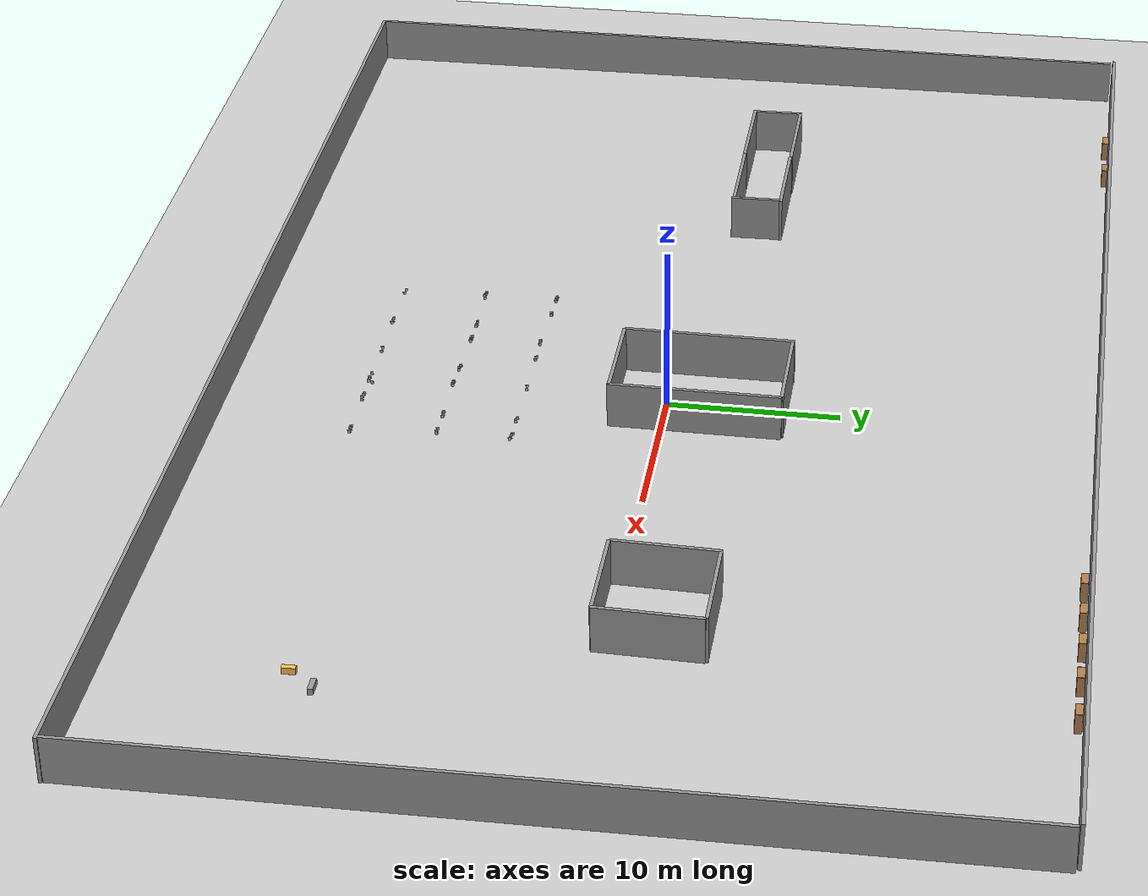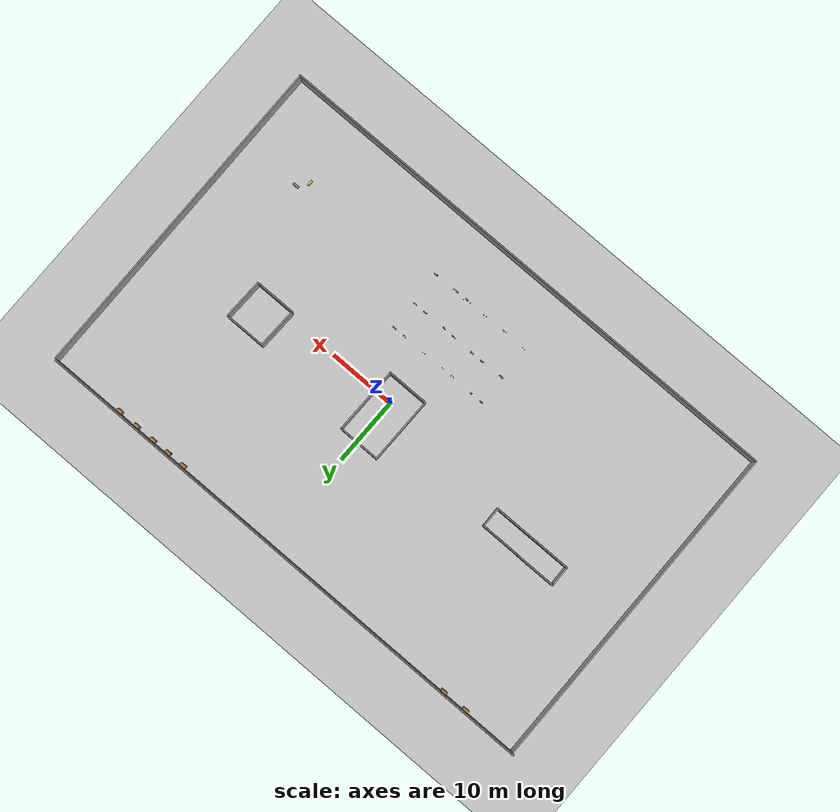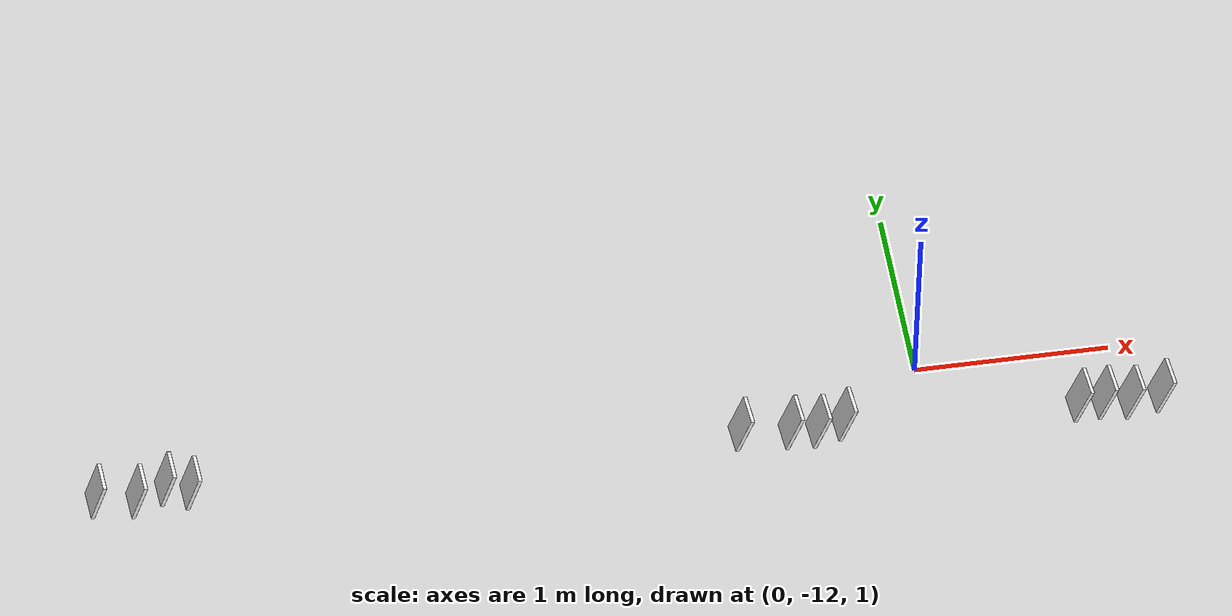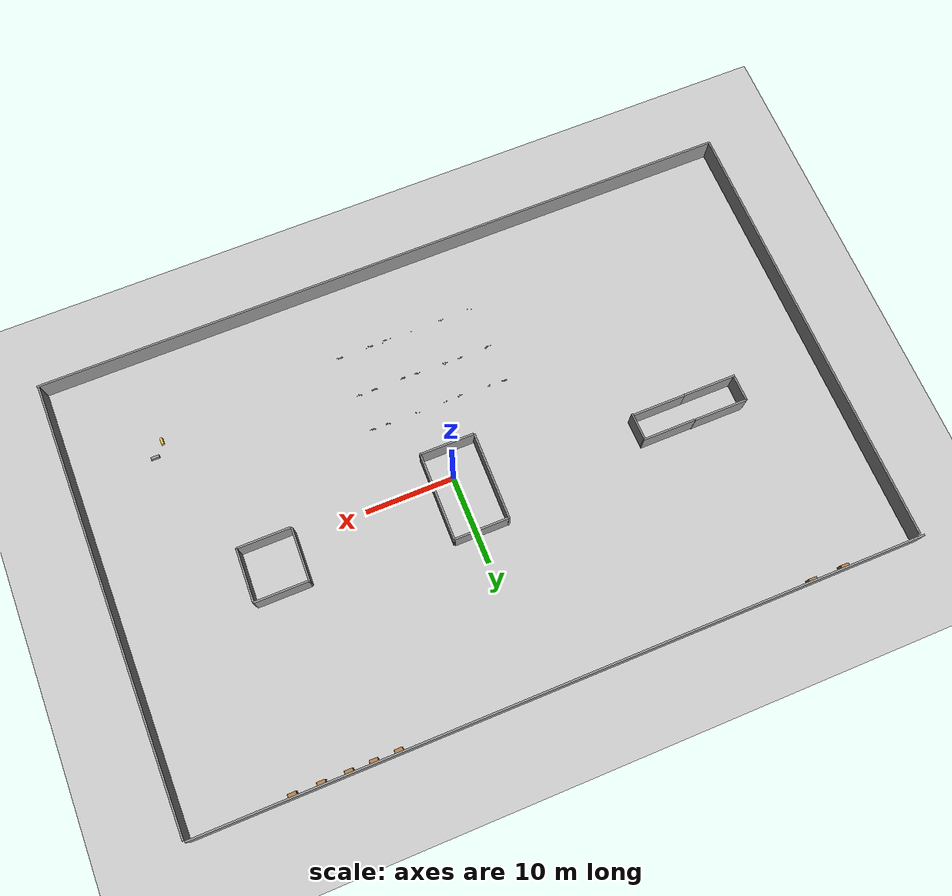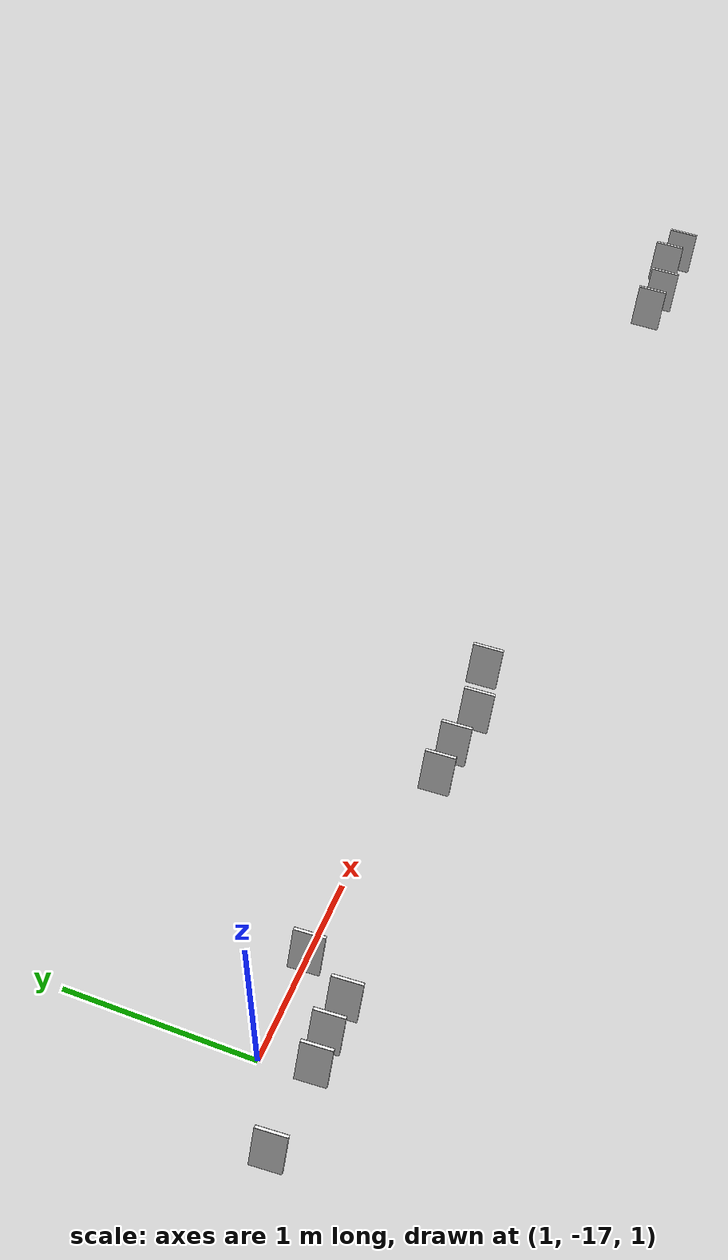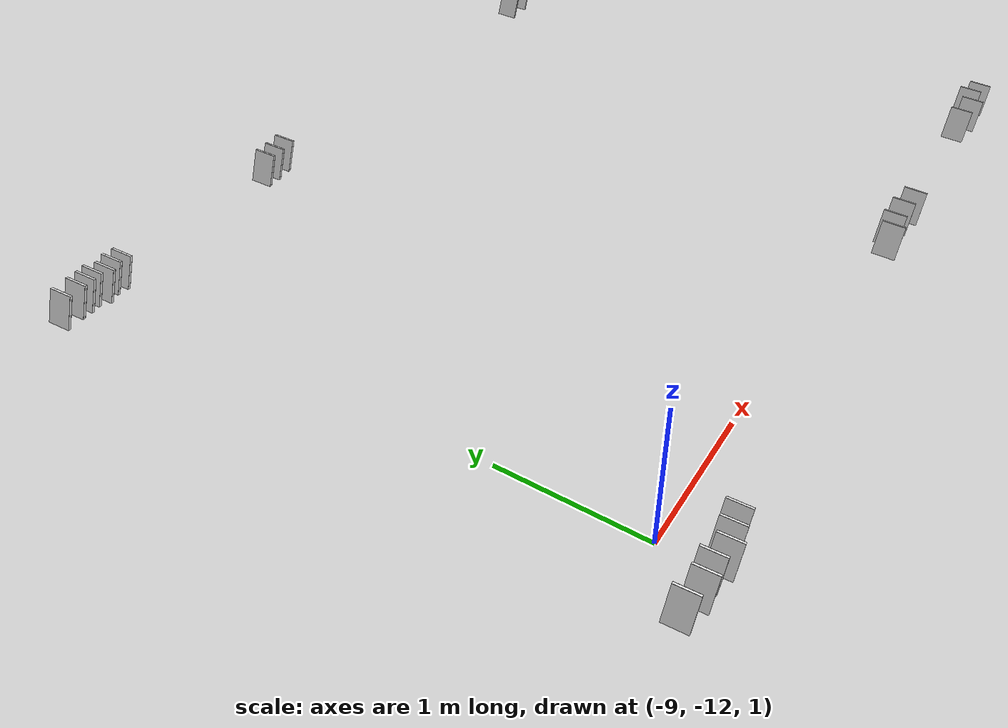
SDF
<sdf version="1.7">
 <world name="default">
  <light name="sun" type="directional">
   <pose>0 0 10 0 -0 0</pose>
   <diffuse>0.8 0.8 0.8 1</diffuse>
   <specular>0.2 0.2 0.2 1</specular>
   <attenuation>
    <range>1000</range>
    <constant>0.9</constant>
    <linear>0.01</linear>
    <quadratic>0.001</quadratic>
   </attenuation>
   <direction>-0.5 0.1 -0.9</direction>
   <spot><inner_angle>0</inner_angle><outer_angle>0</outer_angle><falloff>0</falloff></spot>
  </light>
  <model name="ground_plane">
   <static>1</static>
   <link name="link">
    <collision name="collision">
     <geometry><plane><normal>0 0 1</normal><size>100 100</size></plane></geometry>
     <surface>
      <contact><collide_bitmask>65535</collide_bitmask></contact>
      <friction><ode><mu>100</mu><mu2>50</mu2></ode></friction>
     </surface>
    </collision>
    <visual name="visual">
     <cast_shadows>0</cast_shadows>
     <geometry><plane><normal>0 0 1</normal><size>100 100</size></plane></geometry>
     <material>
      <script><uri>file://media/materials/scripts/gazebo.material</uri><name>Gazebo/Grey</name></script>
     </material>
    </visual>
   </link>
  </model>
  <gravity>0 0 -9.8</gravity>
  <magnetic_field>6e-06 2.3e-05 -4.2e-05</magnetic_field>
  <atmosphere type="adiabatic"/>
  <physics type="ode">
   <max_step_size>0.001</max_step_size>
   <real_time_factor>1</real_time_factor>
   <real_time_update_rate>1000</real_time_update_rate>
  </physics>
  <scene><ambient>0.4 0.4 0.4 1</ambient><background>0.7 0.7 0.7 1</background><shadows>1</shadows></scene>
  <spherical_coordinates>
   <surface_model>EARTH_WGS84</surface_model>
   <latitude_deg>0</latitude_deg>
   <longitude_deg>0</longitude_deg>
   <elevation>0</elevation>
   <heading_deg>0</heading_deg>
  </spherical_coordinates>
  <model name="grey_wall_long">
   <static>1</static>
   <link name="link">
    <pose>0 0 1.4 0 -0 0</pose>
    <collision name="collision"><geometry><box><size>50 0.2 2.8</size></box></geometry></collision>
    <visual name="visual">
     <cast_shadows>0</cast_shadows>
     <geometry><box><size>50 0.2 2.8</size></box></geometry>
     <material>
      <script>
       <uri>model://grey_wall_long/materials/scripts</uri>
       <uri>model://grey_wall_long/materials/textures</uri>
       <name>vrc/grey_wall_long</name>
      </script>
     </material>
    </visual>
   </link>
   <pose>-42.0584 -0.541294 0 0 0 -1.56707</pose>
  </model>
  <model name="grey_wall_long_2">
   <static>1</static>
   <link name="link">
    <pose>0 0 1.4 0 -0 0</pose>
    <collision name="collision"><geometry><box><size>80 0.2 2.8</size></box></geometry></collision>
    <visual name="visual">
     <cast_shadows>0</cast_shadows>
     <geometry><box><size>80 0.2 2.8</size></box></geometry>
     <material>
      <script>
       <uri>model://grey_wall_long_2/materials/scripts</uri>
       <uri>model://grey_wall_long_2/materials/textures</uri>
       <name>vrc/grey_wall_long_2</name>
      </script>
     </material>
    </visual>
   </link>
   <pose>-2.04766 -25.566 0 0 -0 0</pose>
  </model>
  <model name="grey_wall_long_clone">
   <static>1</static>
   <link name="link">
    <pose>0 0 1.4 0 -0 0</pose>
    <collision name="collision"><geometry><box><size>50 0.2 2.8</size></box></geometry></collision>
    <visual name="visual">
     <cast_shadows>0</cast_shadows>
     <geometry><box><size>50 0.2 2.8</size></box></geometry>
     <material>
      <script>
       <uri>model://grey_wall_long/materials/scripts</uri>
       <uri>model://grey_wall_long/materials/textures</uri>
       <name>vrc/grey_wall_long</name>
      </script>
     </material>
    </visual>
   </link>
   <pose>37.6995 -0.475096 0 0 0 -1.56707</pose>
  </model>
  <model name="grey_wall_long_2_clone">
   <static>1</static>
   <link name="link">
    <pose>0 0 1.4 0 -0 0</pose>
    <collision name="collision"><geometry><box><size>80 0.2 2.8</size></box></geometry></collision>
    <visual name="visual">
     <cast_shadows>0</cast_shadows>
     <geometry><box><size>80 0.2 2.8</size></box></geometry>
     <material>
      <script>
       <uri>model://grey_wall_long_2/materials/scripts</uri>
       <uri>model://grey_wall_long_2/materials/textures</uri>
       <name>vrc/grey_wall_long_2</name>
      </script>
     </material>
    </visual>
   </link>
   <pose>-2.52951 24.6852 0 0 -0 0</pose>
  </model>
  <model name="grey_wall_short_2">
   <static>1</static>
   <link name="link">
    <pose>0 0 1.4 0 -0 0</pose>
    <collision name="collision"><geometry><box><size>10 0.2 2.8</size></box></geometry></collision>
    <visual name="visual">
     <cast_shadows>0</cast_shadows>
     <geometry><box><size>10 0.2 2.8</size></box></geometry>
     <material>
      <script>
       <uri>model://grey_wall_short_2/materials/scripts</uri>
       <uri>model://grey_wall_short_2/materials/textures</uri>
       <name>vrc/grey_wall_short_2</name>
      </script>
     </material>
    </visual>
   </link>
   <pose>-3.54745 2.00518 0 0 -0 1.56066</pose>
  </model>
  <model name="grey_wall_short">
   <static>1</static>
   <link name="link">
    <pose>0 0 1.4 0 -0 0</pose>
    <collision name="collision"><geometry><box><size>3 0.2 2.8</size></box></geometry></collision>
    <visual name="visual">
     <cast_shadows>0</cast_shadows>
     <geometry><box><size>3 0.2 2.8</size></box></geometry>
     <material>
      <script>
       <uri>model://grey_wall_short/materials/scripts</uri>
       <uri>model://grey_wall_short/materials/textures</uri>
       <name>vrc/grey_wall_short</name>
      </script>
     </material>
    </visual>
   </link>
   <pose>-32.0114 2.97374 0 0 0 -1.5524</pose>
  </model>
  <model name="grey_wall_media">
   <static>1</static>
   <link name="link">
    <pose>0 0 1.4 0 -0 0</pose>
    <collision name="collision"><geometry><box><size>6 0.2 2.8</size></box></geometry></collision>
    <visual name="visual">
     <cast_shadows>0</cast_shadows>
     <geometry><box><size>6 0.2 2.8</size></box></geometry>
     <material>
      <script>
       <uri>model://grey_wall_media/materials/scripts</uri>
       <uri>model://grey_wall_media/materials/textures</uri>
       <name>vrc/grey_wall_media</name>
      </script>
     </material>
    </visual>
   </link>
   <pose>-29 4.42421 0.00987 0 -0 0</pose>
  </model>
  <model name="grey_wall_media_clone">
   <static>1</static>
   <link name="link">
    <pose>0 0 1.4 0 -0 0</pose>
    <collision name="collision"><geometry><box><size>6 0.2 2.8</size></box></geometry></collision>
    <visual name="visual">
     <cast_shadows>0</cast_shadows>
     <geometry><box><size>6 0.2 2.8</size></box></geometry>
     <material>
      <script>
       <uri>model://grey_wall_media/materials/scripts</uri>
       <uri>model://grey_wall_media/materials/textures</uri>
       <name>vrc/grey_wall_media</name>
      </script>
     </material>
    </visual>
   </link>
   <pose>-23.0062 4.38382 0.00987 0 -0 0</pose>
  </model>
  <model name="grey_wall_short_clone">
   <static>1</static>
   <link name="link">
    <pose>0 0 1.4 0 -0 0</pose>
    <collision name="collision"><geometry><box><size>3 0.2 2.8</size></box></geometry></collision>
    <visual name="visual">
     <cast_shadows>0</cast_shadows>
     <geometry><box><size>3 0.2 2.8</size></box></geometry>
     <material>
      <script>
       <uri>model://grey_wall_short/materials/scripts</uri>
       <uri>model://grey_wall_short/materials/textures</uri>
       <name>vrc/grey_wall_short</name>
      </script>
     </material>
    </visual>
   </link>
   <pose>-20.0584 2.81156 0.06642 0 0 -1.5524</pose>
  </model>
  <model name="grey_wall_media_clone_0">
   <static>1</static>
   <link name="link">
    <pose>0 0 1.4 0 -0 0</pose>
    <collision name="collision"><geometry><box><size>6 0.2 2.8</size></box></geometry></collision>
    <visual name="visual">
     <cast_shadows>0</cast_shadows>
     <geometry><box><size>6 0.2 2.8</size></box></geometry>
     <material>
      <script>
       <uri>model://grey_wall_media/materials/scripts</uri>
       <uri>model://grey_wall_media/materials/textures</uri>
       <name>vrc/grey_wall_media</name>
      </script>
     </material>
    </visual>
   </link>
   <pose>-29.0686 1.44223 0.00987 0 -0 0</pose>
  </model>
  <model name="grey_wall_media_clone_1">
   <static>1</static>
   <link name="link">
    <pose>0 0 1.4 0 -0 0</pose>
    <collision name="collision"><geometry><box><size>6 0.2 2.8</size></box></geometry></collision>
    <visual name="visual">
     <cast_shadows>0</cast_shadows>
     <geometry><box><size>6 0.2 2.8</size></box></geometry>
     <material>
      <script>
       <uri>model://grey_wall_media/materials/scripts</uri>
       <uri>model://grey_wall_media/materials/textures</uri>
       <name>vrc/grey_wall_media</name>
      </script>
     </material>
    </visual>
   </link>
   <pose>-23.1024 1.45669 0.00987 0 -0 0</pose>
  </model>
  <model name="grey_wall_media_clone_2">
   <static>1</static>
   <link name="link">
    <pose>0 0 1.4 0 -0 0</pose>
    <collision name="collision"><geometry><box><size>6 0.2 2.8</size></box></geometry></collision>
    <visual name="visual">
     <cast_shadows>0</cast_shadows>
     <geometry><box><size>6 0.2 2.8</size></box></geometry>
     <material>
      <script>
       <uri>model://grey_wall_media/materials/scripts</uri>
       <uri>model://grey_wall_media/materials/textures</uri>
       <name>vrc/grey_wall_media</name>
      </script>
     </material>
    </visual>
   </link>
   <pose>-0.524154 -3.00144 0.00987 0 -0 0</pose>
  </model>
  <model name="grey_wall_media_clone_3">
   <static>1</static>
   <link name="link">
    <pose>0 0 1.4 0 -0 0</pose>
    <collision name="collision"><geometry><box><size>6 0.2 2.8</size></box></geometry></collision>
    <visual name="visual">
     <cast_shadows>0</cast_shadows>
     <geometry><box><size>6 0.2 2.8</size></box></geometry>
     <material>
      <script>
       <uri>model://grey_wall_media/materials/scripts</uri>
       <uri>model://grey_wall_media/materials/textures</uri>
       <name>vrc/grey_wall_media</name>
      </script>
     </material>
    </visual>
   </link>
   <pose>-0.415049 6.87765 0.00987 0 -0 0</pose>
  </model>
  <model name="grey_wall_short_2_clone">
   <static>1</static>
   <link name="link">
    <pose>0 0 1.4 0 -0 0</pose>
    <collision name="collision"><geometry><box><size>10 0.2 2.8</size></box></geometry></collision>
    <visual name="visual">
     <cast_shadows>0</cast_shadows>
     <geometry><box><size>10 0.2 2.8</size></box></geometry>
     <material>
      <script>
       <uri>model://grey_wall_short_2/materials/scripts</uri>
       <uri>model://grey_wall_short_2/materials/textures</uri>
       <name>vrc/grey_wall_short_2</name>
      </script>
     </material>
    </visual>
   </link>
   <pose>2.57651 1.88532 0 0 -0 1.56066</pose>
  </model>
  <model name="grey_wall_media_clone_2_clone">
   <static>1</static>
   <link name="link">
    <pose>0 0 1.4 0 -0 0</pose>
    <collision name="collision"><geometry><box><size>6 0.2 2.8</size></box></geometry></collision>
    <visual name="visual">
     <cast_shadows>0</cast_shadows>
     <geometry><box><size>6 0.2 2.8</size></box></geometry>
     <material>
      <script>
       <uri>model://grey_wall_media/materials/scripts</uri>
       <uri>model://grey_wall_media/materials/textures</uri>
       <name>vrc/grey_wall_media</name>
      </script>
     </material>
    </visual>
   </link>
   <pose>20.7771 -0.668211 0.00987 0 -0 0</pose>
  </model>
  <model name="grey_wall_media_clone_2_clone_clone">
   <static>1</static>
   <link name="link">
    <pose>0 0 1.4 0 -0 0</pose>
    <collision name="collision"><geometry><box><size>6 0.2 2.8</size></box></geometry></collision>
    <visual name="visual">
     <cast_shadows>0</cast_shadows>
     <geometry><box><size>6 0.2 2.8</size></box></geometry>
     <material>
      <script>
       <uri>model://grey_wall_media/materials/scripts</uri>
       <uri>model://grey_wall_media/materials/textures</uri>
       <name>vrc/grey_wall_media</name>
      </script>
     </material>
    </visual>
   </link>
   <pose>20.9663 5.32207 0.00987 0 -0 0</pose>
  </model>
  <model name="grey_wall_media_clone_2_clone_clone_0">
   <static>1</static>
   <link name="link">
    <pose>0 0 1.4 0 -0 0</pose>
    <collision name="collision"><geometry><box><size>6 0.2 2.8</size></box></geometry></collision>
    <visual name="visual">
     <cast_shadows>0</cast_shadows>
     <geometry><box><size>6 0.2 2.8</size></box></geometry>
     <material>
      <script>
       <uri>model://grey_wall_media/materials/scripts</uri>
       <uri>model://grey_wall_media/materials/textures</uri>
       <name>vrc/grey_wall_media</name>
      </script>
     </material>
    </visual>
   </link>
   <pose>17.8444 2.39168 0.00987 0 0 -1.60343</pose>
  </model>
  <model name="grey_wall_media_clone_2_clone_clone_0_clone">
   <static>1</static>
   <link name="link">
    <pose>0 0 1.4 0 -0 0</pose>
    <collision name="collision"><geometry><box><size>6 0.2 2.8</size></box></geometry></collision>
    <visual name="visual">
     <cast_shadows>0</cast_shadows>
     <geometry><box><size>6 0.2 2.8</size></box></geometry>
     <material>
      <script>
       <uri>model://grey_wall_media/materials/scripts</uri>
       <uri>model://grey_wall_media/materials/textures</uri>
       <name>vrc/grey_wall_media</name>
      </script>
     </material>
    </visual>
   </link>
   <pose>23.857 2.28002 0.00987 0 0 -1.60343</pose>
  </model>
  <model name="Bookshelf">
   <static>1</static>
   <link name="link">
    <inertial><mass>1</mass></inertial>
    <collision name="back">
     <pose>0 0.005 0.6 0 -0 0</pose>
     <geometry><box><size>0.9 0.01 1.2</size></box></geometry>
    </collision>
    <visual name="visual1">
     <pose>0 0.005 0.6 0 -0 0</pose>
     <geometry><box><size>0.9 0.01 1.2</size></box></geometry>
     <material>
      <diffuse>1 1 1 1</diffuse>
      <script><uri>file://media/materials/scripts/gazebo.material</uri><name>Gazebo/Wood</name></script>
      <pbr><metal><albedo_map>model://Bookshelf/bookshelf_diffuse.jpg</albedo_map></metal></pbr>
     </material>
    </visual>
    <collision name="left_side">
     <pose>0.45 -0.195 0.6 0 -0 0</pose>
     <geometry><box><size>0.02 0.4 1.2</size></box></geometry>
    </collision>
    <visual name="visual2">
     <pose>0.45 -0.195 0.6 0 -0 0</pose>
     <geometry><box><size>0.02 0.4 1.2</size></box></geometry>
     <material>
      <diffuse>1 1 1 1</diffuse>
      <script><uri>file://media/materials/scripts/gazebo.material</uri><name>Gazebo/Wood</name></script>
      <pbr><metal><albedo_map>model://Bookshelf/bookshelf_diffuse.jpg</albedo_map></metal></pbr>
     </material>
    </visual>
    <collision name="right_side">
     <pose>-0.45 -0.195 0.6 0 -0 0</pose>
     <geometry><box><size>0.02 0.4 1.2</size></box></geometry>
    </collision>
    <visual name="visual3">
     <pose>-0.45 -0.195 0.6 0 -0 0</pose>
     <geometry><box><size>0.02 0.4 1.2</size></box></geometry>
     <material>
      <diffuse>1 1 1 1</diffuse>
      <script><uri>file://media/materials/scripts/gazebo.material</uri><name>Gazebo/Wood</name></script>
      <pbr><metal><albedo_map>model://Bookshelf/bookshelf_diffuse.jpg</albedo_map></metal></pbr>
     </material>
    </visual>
    <collision name="bottom">
     <pose>0 -0.195 0.03 0 -0 0</pose>
     <geometry><box><size>0.88 0.4 0.06</size></box></geometry>
    </collision>
    <visual name="visual4">
     <pose>0 -0.195 0.03 0 -0 0</pose>
     <geometry><box><size>0.88 0.4 0.06</size></box></geometry>
     <material>
      <diffuse>1 1 1 1</diffuse>
      <script><uri>file://media/materials/scripts/gazebo.material</uri><name>Gazebo/Wood</name></script>
      <pbr><metal><albedo_map>model://Bookshelf/bookshelf_diffuse.jpg</albedo_map></metal></pbr>
     </material>
    </visual>
    <collision name="top">
     <pose>0 -0.195 1.19 0 -0 0</pose>
     <geometry><box><size>0.88 0.4 0.02</size></box></geometry>
    </collision>
    <visual name="visual5">
     <pose>0 -0.195 1.19 0 -0 0</pose>
     <geometry><box><size>0.88 0.4 0.02</size></box></geometry>
     <material>
      <diffuse>1 1 1 1</diffuse>
      <script><uri>file://media/materials/scripts/gazebo.material</uri><name>Gazebo/Wood</name></script>
      <pbr><metal><albedo_map>model://Bookshelf/bookshelf_diffuse.jpg</albedo_map></metal></pbr>
     </material>
    </visual>
    <collision name="low_shelf">
     <pose>0 -0.195 0.43 0 -0 0</pose>
     <geometry><box><size>0.88 0.4 0.02</size></box></geometry>
    </collision>
    <visual name="visual6">
     <pose>0 -0.195 0.43 0 -0 0</pose>
     <geometry><box><size>0.88 0.4 0.02</size></box></geometry>
     <material>
      <diffuse>1 1 1 1</diffuse>
      <script><uri>file://media/materials/scripts/gazebo.material</uri><name>Gazebo/Wood</name></script>
      <pbr><metal><albedo_map>model://Bookshelf/bookshelf_diffuse.jpg</albedo_map></metal></pbr>
     </material>
    </visual>
    <collision name="high_shelf">
     <pose>0 -0.195 0.8 0 -0 0</pose>
     <geometry><box><size>0.88 0.4 0.02</size></box></geometry>
    </collision>
    <visual name="visual7">
     <pose>0 -0.195 0.8 0 -0 0</pose>
     <geometry><box><size>0.88 0.4 0.02</size></box></geometry>
     <material>
      <diffuse>1 1 1 1</diffuse>
      <script><uri>file://media/materials/scripts/gazebo.material</uri><name>Gazebo/Wood</name></script>
      <pbr><metal><albedo_map>model://Bookshelf/bookshelf_diffuse.jpg</albedo_map></metal></pbr>
     </material>
    </visual>
   </link>
   <pose>-30.3238 24.6424 -0.021454 0 -0 0</pose>
  </model>
  <model name="Bookshelf_0">
   <static>1</static>
   <link name="link">
    <inertial><mass>1</mass></inertial>
    <collision name="back">
     <pose>0 0.005 0.6 0 -0 0</pose>
     <geometry><box><size>0.9 0.01 1.2</size></box></geometry>
    </collision>
    <visual name="visual1">
     <pose>0 0.005 0.6 0 -0 0</pose>
     <geometry><box><size>0.9 0.01 1.2</size></box></geometry>
     <material>
      <diffuse>1 1 1 1</diffuse>
      <script><uri>file://media/materials/scripts/gazebo.material</uri><name>Gazebo/Wood</name></script>
      <pbr><metal><albedo_map>model://Bookshelf/bookshelf_diffuse.jpg</albedo_map></metal></pbr>
     </material>
    </visual>
    <collision name="left_side">
     <pose>0.45 -0.195 0.6 0 -0 0</pose>
     <geometry><box><size>0.02 0.4 1.2</size></box></geometry>
    </collision>
    <visual name="visual2">
     <pose>0.45 -0.195 0.6 0 -0 0</pose>
     <geometry><box><size>0.02 0.4 1.2</size></box></geometry>
     <material>
      <diffuse>1 1 1 1</diffuse>
      <script><uri>file://media/materials/scripts/gazebo.material</uri><name>Gazebo/Wood</name></script>
      <pbr><metal><albedo_map>model://Bookshelf/bookshelf_diffuse.jpg</albedo_map></metal></pbr>
     </material>
    </visual>
    <collision name="right_side">
     <pose>-0.45 -0.195 0.6 0 -0 0</pose>
     <geometry><box><size>0.02 0.4 1.2</size></box></geometry>
    </collision>
    <visual name="visual3">
     <pose>-0.45 -0.195 0.6 0 -0 0</pose>
     <geometry><box><size>0.02 0.4 1.2</size></box></geometry>
     <material>
      <diffuse>1 1 1 1</diffuse>
      <script><uri>file://media/materials/scripts/gazebo.material</uri><name>Gazebo/Wood</name></script>
      <pbr><metal><albedo_map>model://Bookshelf/bookshelf_diffuse.jpg</albedo_map></metal></pbr>
     </material>
    </visual>
    <collision name="bottom">
     <pose>0 -0.195 0.03 0 -0 0</pose>
     <geometry><box><size>0.88 0.4 0.06</size></box></geometry>
    </collision>
    <visual name="visual4">
     <pose>0 -0.195 0.03 0 -0 0</pose>
     <geometry><box><size>0.88 0.4 0.06</size></box></geometry>
     <material>
      <diffuse>1 1 1 1</diffuse>
      <script><uri>file://media/materials/scripts/gazebo.material</uri><name>Gazebo/Wood</name></script>
      <pbr><metal><albedo_map>model://Bookshelf/bookshelf_diffuse.jpg</albedo_map></metal></pbr>
     </material>
    </visual>
    <collision name="top">
     <pose>0 -0.195 1.19 0 -0 0</pose>
     <geometry><box><size>0.88 0.4 0.02</size></box></geometry>
    </collision>
    <visual name="visual5">
     <pose>0 -0.195 1.19 0 -0 0</pose>
     <geometry><box><size>0.88 0.4 0.02</size></box></geometry>
     <material>
      <diffuse>1 1 1 1</diffuse>
      <script><uri>file://media/materials/scripts/gazebo.material</uri><name>Gazebo/Wood</name></script>
      <pbr><metal><albedo_map>model://Bookshelf/bookshelf_diffuse.jpg</albedo_map></metal></pbr>
     </material>
    </visual>
    <collision name="low_shelf">
     <pose>0 -0.195 0.43 0 -0 0</pose>
     <geometry><box><size>0.88 0.4 0.02</size></box></geometry>
    </collision>
    <visual name="visual6">
     <pose>0 -0.195 0.43 0 -0 0</pose>
     <geometry><box><size>0.88 0.4 0.02</size></box></geometry>
     <material>
      <diffuse>1 1 1 1</diffuse>
      <script><uri>file://media/materials/scripts/gazebo.material</uri><name>Gazebo/Wood</name></script>
      <pbr><metal><albedo_map>model://Bookshelf/bookshelf_diffuse.jpg</albedo_map></metal></pbr>
     </material>
    </visual>
    <collision name="high_shelf">
     <pose>0 -0.195 0.8 0 -0 0</pose>
     <geometry><box><size>0.88 0.4 0.02</size></box></geometry>
    </collision>
    <visual name="visual7">
     <pose>0 -0.195 0.8 0 -0 0</pose>
     <geometry><box><size>0.88 0.4 0.02</size></box></geometry>
     <material>
      <diffuse>1 1 1 1</diffuse>
      <script><uri>file://media/materials/scripts/gazebo.material</uri><name>Gazebo/Wood</name></script>
      <pbr><metal><albedo_map>model://Bookshelf/bookshelf_diffuse.jpg</albedo_map></metal></pbr>
     </material>
    </visual>
   </link>
   <pose>26.7566 24.5208 0 0 -0 0</pose>
  </model>
  <model name="Bookshelf_0_clone">
   <static>1</static>
   <link name="link">
    <inertial><mass>1</mass></inertial>
    <collision name="back">
     <pose>0 0.005 0.6 0 -0 0</pose>
     <geometry><box><size>0.9 0.01 1.2</size></box></geometry>
    </collision>
    <visual name="visual1">
     <pose>0 0.005 0.6 0 -0 0</pose>
     <geometry><box><size>0.9 0.01 1.2</size></box></geometry>
     <material>
      <diffuse>1 1 1 1</diffuse>
      <script><uri>file://media/materials/scripts/gazebo.material</uri><name>Gazebo/Wood</name></script>
      <pbr><metal><albedo_map>model://Bookshelf/bookshelf_diffuse.jpg</albedo_map></metal></pbr>
     </material>
    </visual>
    <collision name="left_side">
     <pose>0.45 -0.195 0.6 0 -0 0</pose>
     <geometry><box><size>0.02 0.4 1.2</size></box></geometry>
    </collision>
    <visual name="visual2">
     <pose>0.45 -0.195 0.6 0 -0 0</pose>
     <geometry><box><size>0.02 0.4 1.2</size></box></geometry>
     <material>
      <diffuse>1 1 1 1</diffuse>
      <script><uri>file://media/materials/scripts/gazebo.material</uri><name>Gazebo/Wood</name></script>
      <pbr><metal><albedo_map>model://Bookshelf/bookshelf_diffuse.jpg</albedo_map></metal></pbr>
     </material>
    </visual>
    <collision name="right_side">
     <pose>-0.45 -0.195 0.6 0 -0 0</pose>
     <geometry><box><size>0.02 0.4 1.2</size></box></geometry>
    </collision>
    <visual name="visual3">
     <pose>-0.45 -0.195 0.6 0 -0 0</pose>
     <geometry><box><size>0.02 0.4 1.2</size></box></geometry>
     <material>
      <diffuse>1 1 1 1</diffuse>
      <script><uri>file://media/materials/scripts/gazebo.material</uri><name>Gazebo/Wood</name></script>
      <pbr><metal><albedo_map>model://Bookshelf/bookshelf_diffuse.jpg</albedo_map></metal></pbr>
     </material>
    </visual>
    <collision name="bottom">
     <pose>0 -0.195 0.03 0 -0 0</pose>
     <geometry><box><size>0.88 0.4 0.06</size></box></geometry>
    </collision>
    <visual name="visual4">
     <pose>0 -0.195 0.03 0 -0 0</pose>
     <geometry><box><size>0.88 0.4 0.06</size></box></geometry>
     <material>
      <diffuse>1 1 1 1</diffuse>
      <script><uri>file://media/materials/scripts/gazebo.material</uri><name>Gazebo/Wood</name></script>
      <pbr><metal><albedo_map>model://Bookshelf/bookshelf_diffuse.jpg</albedo_map></metal></pbr>
     </material>
    </visual>
    <collision name="top">
     <pose>0 -0.195 1.19 0 -0 0</pose>
     <geometry><box><size>0.88 0.4 0.02</size></box></geometry>
    </collision>
    <visual name="visual5">
     <pose>0 -0.195 1.19 0 -0 0</pose>
     <geometry><box><size>0.88 0.4 0.02</size></box></geometry>
     <material>
      <diffuse>1 1 1 1</diffuse>
      <script><uri>file://media/materials/scripts/gazebo.material</uri><name>Gazebo/Wood</name></script>
      <pbr><metal><albedo_map>model://Bookshelf/bookshelf_diffuse.jpg</albedo_map></metal></pbr>
     </material>
    </visual>
    <collision name="low_shelf">
     <pose>0 -0.195 0.43 0 -0 0</pose>
     <geometry><box><size>0.88 0.4 0.02</size></box></geometry>
    </collision>
    <visual name="visual6">
     <pose>0 -0.195 0.43 0 -0 0</pose>
     <geometry><box><size>0.88 0.4 0.02</size></box></geometry>
     <material>
      <diffuse>1 1 1 1</diffuse>
      <script><uri>file://media/materials/scripts/gazebo.material</uri><name>Gazebo/Wood</name></script>
      <pbr><metal><albedo_map>model://Bookshelf/bookshelf_diffuse.jpg</albedo_map></metal></pbr>
     </material>
    </visual>
    <collision name="high_shelf">
     <pose>0 -0.195 0.8 0 -0 0</pose>
     <geometry><box><size>0.88 0.4 0.02</size></box></geometry>
    </collision>
    <visual name="visual7">
     <pose>0 -0.195 0.8 0 -0 0</pose>
     <geometry><box><size>0.88 0.4 0.02</size></box></geometry>
     <material>
      <diffuse>1 1 1 1</diffuse>
      <script><uri>file://media/materials/scripts/gazebo.material</uri><name>Gazebo/Wood</name></script>
      <pbr><metal><albedo_map>model://Bookshelf/bookshelf_diffuse.jpg</albedo_map></metal></pbr>
     </material>
    </visual>
   </link>
   <pose>23.7282 24.54 0 0 -0 0</pose>
  </model>
  <model name="Bookshelf_0_clone_0">
   <static>1</static>
   <link name="link">
    <inertial><mass>1</mass></inertial>
    <collision name="back">
     <pose>0 0.005 0.6 0 -0 0</pose>
     <geometry><box><size>0.9 0.01 1.2</size></box></geometry>
    </collision>
    <visual name="visual1">
     <pose>0 0.005 0.6 0 -0 0</pose>
     <geometry><box><size>0.9 0.01 1.2</size></box></geometry>
     <material>
      <diffuse>1 1 1 1</diffuse>
      <script><uri>file://media/materials/scripts/gazebo.material</uri><name>Gazebo/Wood</name></script>
      <pbr><metal><albedo_map>model://Bookshelf/bookshelf_diffuse.jpg</albedo_map></metal></pbr>
     </material>
    </visual>
    <collision name="left_side">
     <pose>0.45 -0.195 0.6 0 -0 0</pose>
     <geometry><box><size>0.02 0.4 1.2</size></box></geometry>
    </collision>
    <visual name="visual2">
     <pose>0.45 -0.195 0.6 0 -0 0</pose>
     <geometry><box><size>0.02 0.4 1.2</size></box></geometry>
     <material>
      <diffuse>1 1 1 1</diffuse>
      <script><uri>file://media/materials/scripts/gazebo.material</uri><name>Gazebo/Wood</name></script>
      <pbr><metal><albedo_map>model://Bookshelf/bookshelf_diffuse.jpg</albedo_map></metal></pbr>
     </material>
    </visual>
    <collision name="right_side">
     <pose>-0.45 -0.195 0.6 0 -0 0</pose>
     <geometry><box><size>0.02 0.4 1.2</size></box></geometry>
    </collision>
    <visual name="visual3">
     <pose>-0.45 -0.195 0.6 0 -0 0</pose>
     <geometry><box><size>0.02 0.4 1.2</size></box></geometry>
     <material>
      <diffuse>1 1 1 1</diffuse>
      <script><uri>file://media/materials/scripts/gazebo.material</uri><name>Gazebo/Wood</name></script>
      <pbr><metal><albedo_map>model://Bookshelf/bookshelf_diffuse.jpg</albedo_map></metal></pbr>
     </material>
    </visual>
    <collision name="bottom">
     <pose>0 -0.195 0.03 0 -0 0</pose>
     <geometry><box><size>0.88 0.4 0.06</size></box></geometry>
    </collision>
    <visual name="visual4">
     <pose>0 -0.195 0.03 0 -0 0</pose>
     <geometry><box><size>0.88 0.4 0.06</size></box></geometry>
     <material>
      <diffuse>1 1 1 1</diffuse>
      <script><uri>file://media/materials/scripts/gazebo.material</uri><name>Gazebo/Wood</name></script>
      <pbr><metal><albedo_map>model://Bookshelf/bookshelf_diffuse.jpg</albedo_map></metal></pbr>
     </material>
    </visual>
    <collision name="top">
     <pose>0 -0.195 1.19 0 -0 0</pose>
     <geometry><box><size>0.88 0.4 0.02</size></box></geometry>
    </collision>
    <visual name="visual5">
     <pose>0 -0.195 1.19 0 -0 0</pose>
     <geometry><box><size>0.88 0.4 0.02</size></box></geometry>
     <material>
      <diffuse>1 1 1 1</diffuse>
      <script><uri>file://media/materials/scripts/gazebo.material</uri><name>Gazebo/Wood</name></script>
      <pbr><metal><albedo_map>model://Bookshelf/bookshelf_diffuse.jpg</albedo_map></metal></pbr>
     </material>
    </visual>
    <collision name="low_shelf">
     <pose>0 -0.195 0.43 0 -0 0</pose>
     <geometry><box><size>0.88 0.4 0.02</size></box></geometry>
    </collision>
    <visual name="visual6">
     <pose>0 -0.195 0.43 0 -0 0</pose>
     <geometry><box><size>0.88 0.4 0.02</size></box></geometry>
     <material>
      <diffuse>1 1 1 1</diffuse>
      <script><uri>file://media/materials/scripts/gazebo.material</uri><name>Gazebo/Wood</name></script>
      <pbr><metal><albedo_map>model://Bookshelf/bookshelf_diffuse.jpg</albedo_map></metal></pbr>
     </material>
    </visual>
    <collision name="high_shelf">
     <pose>0 -0.195 0.8 0 -0 0</pose>
     <geometry><box><size>0.88 0.4 0.02</size></box></geometry>
    </collision>
    <visual name="visual7">
     <pose>0 -0.195 0.8 0 -0 0</pose>
     <geometry><box><size>0.88 0.4 0.02</size></box></geometry>
     <material>
      <diffuse>1 1 1 1</diffuse>
      <script><uri>file://media/materials/scripts/gazebo.material</uri><name>Gazebo/Wood</name></script>
      <pbr><metal><albedo_map>model://Bookshelf/bookshelf_diffuse.jpg</albedo_map></metal></pbr>
     </material>
    </visual>
   </link>
   <pose>20.8419 24.5504 0 0 -0 0</pose>
  </model>
  <model name="Bookshelf_0_clone_1">
   <static>1</static>
   <link name="link">
    <inertial><mass>1</mass></inertial>
    <collision name="back">
     <pose>0 0.005 0.6 0 -0 0</pose>
     <geometry><box><size>0.9 0.01 1.2</size></box></geometry>
    </collision>
    <visual name="visual1">
     <pose>0 0.005 0.6 0 -0 0</pose>
     <geometry><box><size>0.9 0.01 1.2</size></box></geometry>
     <material>
      <diffuse>1 1 1 1</diffuse>
      <script><uri>file://media/materials/scripts/gazebo.material</uri><name>Gazebo/Wood</name></script>
      <pbr><metal><albedo_map>model://Bookshelf/bookshelf_diffuse.jpg</albedo_map></metal></pbr>
     </material>
    </visual>
    <collision name="left_side">
     <pose>0.45 -0.195 0.6 0 -0 0</pose>
     <geometry><box><size>0.02 0.4 1.2</size></box></geometry>
    </collision>
    <visual name="visual2">
     <pose>0.45 -0.195 0.6 0 -0 0</pose>
     <geometry><box><size>0.02 0.4 1.2</size></box></geometry>
     <material>
      <diffuse>1 1 1 1</diffuse>
      <script><uri>file://media/materials/scripts/gazebo.material</uri><name>Gazebo/Wood</name></script>
      <pbr><metal><albedo_map>model://Bookshelf/bookshelf_diffuse.jpg</albedo_map></metal></pbr>
     </material>
    </visual>
    <collision name="right_side">
     <pose>-0.45 -0.195 0.6 0 -0 0</pose>
     <geometry><box><size>0.02 0.4 1.2</size></box></geometry>
    </collision>
    <visual name="visual3">
     <pose>-0.45 -0.195 0.6 0 -0 0</pose>
     <geometry><box><size>0.02 0.4 1.2</size></box></geometry>
     <material>
      <diffuse>1 1 1 1</diffuse>
      <script><uri>file://media/materials/scripts/gazebo.material</uri><name>Gazebo/Wood</name></script>
      <pbr><metal><albedo_map>model://Bookshelf/bookshelf_diffuse.jpg</albedo_map></metal></pbr>
     </material>
    </visual>
    <collision name="bottom">
     <pose>0 -0.195 0.03 0 -0 0</pose>
     <geometry><box><size>0.88 0.4 0.06</size></box></geometry>
    </collision>
    <visual name="visual4">
     <pose>0 -0.195 0.03 0 -0 0</pose>
     <geometry><box><size>0.88 0.4 0.06</size></box></geometry>
     <material>
      <diffuse>1 1 1 1</diffuse>
      <script><uri>file://media/materials/scripts/gazebo.material</uri><name>Gazebo/Wood</name></script>
      <pbr><metal><albedo_map>model://Bookshelf/bookshelf_diffuse.jpg</albedo_map></metal></pbr>
     </material>
    </visual>
    <collision name="top">
     <pose>0 -0.195 1.19 0 -0 0</pose>
     <geometry><box><size>0.88 0.4 0.02</size></box></geometry>
    </collision>
    <visual name="visual5">
     <pose>0 -0.195 1.19 0 -0 0</pose>
     <geometry><box><size>0.88 0.4 0.02</size></box></geometry>
     <material>
      <diffuse>1 1 1 1</diffuse>
      <script><uri>file://media/materials/scripts/gazebo.material</uri><name>Gazebo/Wood</name></script>
      <pbr><metal><albedo_map>model://Bookshelf/bookshelf_diffuse.jpg</albedo_map></metal></pbr>
     </material>
    </visual>
    <collision name="low_shelf">
     <pose>0 -0.195 0.43 0 -0 0</pose>
     <geometry><box><size>0.88 0.4 0.02</size></box></geometry>
    </collision>
    <visual name="visual6">
     <pose>0 -0.195 0.43 0 -0 0</pose>
     <geometry><box><size>0.88 0.4 0.02</size></box></geometry>
     <material>
      <diffuse>1 1 1 1</diffuse>
      <script><uri>file://media/materials/scripts/gazebo.material</uri><name>Gazebo/Wood</name></script>
      <pbr><metal><albedo_map>model://Bookshelf/bookshelf_diffuse.jpg</albedo_map></metal></pbr>
     </material>
    </visual>
    <collision name="high_shelf">
     <pose>0 -0.195 0.8 0 -0 0</pose>
     <geometry><box><size>0.88 0.4 0.02</size></box></geometry>
    </collision>
    <visual name="visual7">
     <pose>0 -0.195 0.8 0 -0 0</pose>
     <geometry><box><size>0.88 0.4 0.02</size></box></geometry>
     <material>
      <diffuse>1 1 1 1</diffuse>
      <script><uri>file://media/materials/scripts/gazebo.material</uri><name>Gazebo/Wood</name></script>
      <pbr><metal><albedo_map>model://Bookshelf/bookshelf_diffuse.jpg</albedo_map></metal></pbr>
     </material>
    </visual>
   </link>
   <pose>18.2097 24.5275 0 0 -0 0</pose>
  </model>
  <model name="Bookshelf_0_clone_2">
   <static>1</static>
   <link name="link">
    <inertial><mass>1</mass></inertial>
    <collision name="back">
     <pose>0 0.005 0.6 0 -0 0</pose>
     <geometry><box><size>0.9 0.01 1.2</size></box></geometry>
    </collision>
    <visual name="visual1">
     <pose>0 0.005 0.6 0 -0 0</pose>
     <geometry><box><size>0.9 0.01 1.2</size></box></geometry>
     <material>
      <diffuse>1 1 1 1</diffuse>
      <script><uri>file://media/materials/scripts/gazebo.material</uri><name>Gazebo/Wood</name></script>
      <pbr><metal><albedo_map>model://Bookshelf/bookshelf_diffuse.jpg</albedo_map></metal></pbr>
     </material>
    </visual>
    <collision name="left_side">
     <pose>0.45 -0.195 0.6 0 -0 0</pose>
     <geometry><box><size>0.02 0.4 1.2</size></box></geometry>
    </collision>
    <visual name="visual2">
     <pose>0.45 -0.195 0.6 0 -0 0</pose>
     <geometry><box><size>0.02 0.4 1.2</size></box></geometry>
     <material>
      <diffuse>1 1 1 1</diffuse>
      <script><uri>file://media/materials/scripts/gazebo.material</uri><name>Gazebo/Wood</name></script>
      <pbr><metal><albedo_map>model://Bookshelf/bookshelf_diffuse.jpg</albedo_map></metal></pbr>
     </material>
    </visual>
    <collision name="right_side">
     <pose>-0.45 -0.195 0.6 0 -0 0</pose>
     <geometry><box><size>0.02 0.4 1.2</size></box></geometry>
    </collision>
    <visual name="visual3">
     <pose>-0.45 -0.195 0.6 0 -0 0</pose>
     <geometry><box><size>0.02 0.4 1.2</size></box></geometry>
     <material>
      <diffuse>1 1 1 1</diffuse>
      <script><uri>file://media/materials/scripts/gazebo.material</uri><name>Gazebo/Wood</name></script>
      <pbr><metal><albedo_map>model://Bookshelf/bookshelf_diffuse.jpg</albedo_map></metal></pbr>
     </material>
    </visual>
    <collision name="bottom">
     <pose>0 -0.195 0.03 0 -0 0</pose>
     <geometry><box><size>0.88 0.4 0.06</size></box></geometry>
    </collision>
    <visual name="visual4">
     <pose>0 -0.195 0.03 0 -0 0</pose>
     <geometry><box><size>0.88 0.4 0.06</size></box></geometry>
     <material>
      <diffuse>1 1 1 1</diffuse>
      <script><uri>file://media/materials/scripts/gazebo.material</uri><name>Gazebo/Wood</name></script>
      <pbr><metal><albedo_map>model://Bookshelf/bookshelf_diffuse.jpg</albedo_map></metal></pbr>
     </material>
    </visual>
    <collision name="top">
     <pose>0 -0.195 1.19 0 -0 0</pose>
     <geometry><box><size>0.88 0.4 0.02</size></box></geometry>
    </collision>
    <visual name="visual5">
     <pose>0 -0.195 1.19 0 -0 0</pose>
     <geometry><box><size>0.88 0.4 0.02</size></box></geometry>
     <material>
      <diffuse>1 1 1 1</diffuse>
      <script><uri>file://media/materials/scripts/gazebo.material</uri><name>Gazebo/Wood</name></script>
      <pbr><metal><albedo_map>model://Bookshelf/bookshelf_diffuse.jpg</albedo_map></metal></pbr>
     </material>
    </visual>
    <collision name="low_shelf">
     <pose>0 -0.195 0.43 0 -0 0</pose>
     <geometry><box><size>0.88 0.4 0.02</size></box></geometry>
    </collision>
    <visual name="visual6">
     <pose>0 -0.195 0.43 0 -0 0</pose>
     <geometry><box><size>0.88 0.4 0.02</size></box></geometry>
     <material>
      <diffuse>1 1 1 1</diffuse>
      <script><uri>file://media/materials/scripts/gazebo.material</uri><name>Gazebo/Wood</name></script>
      <pbr><metal><albedo_map>model://Bookshelf/bookshelf_diffuse.jpg</albedo_map></metal></pbr>
     </material>
    </visual>
    <collision name="high_shelf">
     <pose>0 -0.195 0.8 0 -0 0</pose>
     <geometry><box><size>0.88 0.4 0.02</size></box></geometry>
    </collision>
    <visual name="visual7">
     <pose>0 -0.195 0.8 0 -0 0</pose>
     <geometry><box><size>0.88 0.4 0.02</size></box></geometry>
     <material>
      <diffuse>1 1 1 1</diffuse>
      <script><uri>file://media/materials/scripts/gazebo.material</uri><name>Gazebo/Wood</name></script>
      <pbr><metal><albedo_map>model://Bookshelf/bookshelf_diffuse.jpg</albedo_map></metal></pbr>
     </material>
    </visual>
   </link>
   <pose>15.566 24.5124 0 0 -0 0</pose>
  </model>
  <model name="Box_15x30">
   <link name="Wall">
    <pose>0 0 0.1985 0 -0 0</pose>
    <inertial>
     <mass>5</mass>
     <inertia><ixx>0.3089</ixx><iyy>0.1022</iyy><izz>0.2797</izz><ixy>0</ixy><ixz>0</ixz><iyz>0</iyz></inertia>
    </inertial>
    <collision name="Wall_Collision"><geometry><box><size>0.296 0.764 0.397</size></box></geometry></collision>
    <visual name="Wall_Visual">
     <geometry><box><size>0.296 0.764 0.397</size></box></geometry>
     <material>
      <script><uri>file://media/materials/scripts/gazebo.material</uri><name>Gazebo/Grey</name></script>
      <ambient>1 0.764706 0.305882 1</ambient>
     </material>
    </visual>
   </link>
   <static>1</static>
   <pose>27.7034 -15.6588 0 0 -0 0</pose>
  </model>
  <model name="Box_36x15W">
   <link name="Wall">
    <pose>0 0 0.1985 0 -0 0</pose>
    <inertial>
     <mass>5</mass>
     <inertia><ixx>0.1022</ixx><iyy>0.4107</iyy><izz>0.3815</izz><ixy>0</ixy><ixz>0</ixz><iyz>0</iyz></inertia>
    </inertial>
    <collision name="Wall_Collision"><geometry><box><size>0.91 0.296 0.397</size></box></geometry></collision>
    <visual name="Wall_Visual">
     <geometry><box><size>0.91 0.296 0.397</size></box></geometry>
     <material>
      <script><uri>file://media/materials/scripts/gazebo.material</uri><name>Gazebo/Grey</name></script>
      <ambient>1 1 1 1</ambient>
     </material>
    </visual>
   </link>
   <static>1</static>
   <pose>28.9262 -14.1607 0 0 -0 0</pose>
  </model>
  <model name="Bookshelf_clone">
   <static>1</static>
   <link name="link">
    <inertial><mass>1</mass></inertial>
    <collision name="back">
     <pose>0 0.005 0.6 0 -0 0</pose>
     <geometry><box><size>0.9 0.01 1.2</size></box></geometry>
    </collision>
    <visual name="visual1">
     <pose>0 0.005 0.6 0 -0 0</pose>
     <geometry><box><size>0.9 0.01 1.2</size></box></geometry>
     <material>
      <diffuse>1 1 1 1</diffuse>
      <script><uri>file://media/materials/scripts/gazebo.material</uri><name>Gazebo/Wood</name></script>
      <pbr><metal><albedo_map>model://Bookshelf/bookshelf_diffuse.jpg</albedo_map></metal></pbr>
     </material>
    </visual>
    <collision name="left_side">
     <pose>0.45 -0.195 0.6 0 -0 0</pose>
     <geometry><box><size>0.02 0.4 1.2</size></box></geometry>
    </collision>
    <visual name="visual2">
     <pose>0.45 -0.195 0.6 0 -0 0</pose>
     <geometry><box><size>0.02 0.4 1.2</size></box></geometry>
     <material>
      <diffuse>1 1 1 1</diffuse>
      <script><uri>file://media/materials/scripts/gazebo.material</uri><name>Gazebo/Wood</name></script>
      <pbr><metal><albedo_map>model://Bookshelf/bookshelf_diffuse.jpg</albedo_map></metal></pbr>
     </material>
    </visual>
    <collision name="right_side">
     <pose>-0.45 -0.195 0.6 0 -0 0</pose>
     <geometry><box><size>0.02 0.4 1.2</size></box></geometry>
    </collision>
    <visual name="visual3">
     <pose>-0.45 -0.195 0.6 0 -0 0</pose>
     <geometry><box><size>0.02 0.4 1.2</size></box></geometry>
     <material>
      <diffuse>1 1 1 1</diffuse>
      <script><uri>file://media/materials/scripts/gazebo.material</uri><name>Gazebo/Wood</name></script>
      <pbr><metal><albedo_map>model://Bookshelf/bookshelf_diffuse.jpg</albedo_map></metal></pbr>
     </material>
    </visual>
    <collision name="bottom">
     <pose>0 -0.195 0.03 0 -0 0</pose>
     <geometry><box><size>0.88 0.4 0.06</size></box></geometry>
    </collision>
    <visual name="visual4">
     <pose>0 -0.195 0.03 0 -0 0</pose>
     <geometry><box><size>0.88 0.4 0.06</size></box></geometry>
     <material>
      <diffuse>1 1 1 1</diffuse>
      <script><uri>file://media/materials/scripts/gazebo.material</uri><name>Gazebo/Wood</name></script>
      <pbr><metal><albedo_map>model://Bookshelf/bookshelf_diffuse.jpg</albedo_map></metal></pbr>
     </material>
    </visual>
    <collision name="top">
     <pose>0 -0.195 1.19 0 -0 0</pose>
     <geometry><box><size>0.88 0.4 0.02</size></box></geometry>
    </collision>
    <visual name="visual5">
     <pose>0 -0.195 1.19 0 -0 0</pose>
     <geometry><box><size>0.88 0.4 0.02</size></box></geometry>
     <material>
      <diffuse>1 1 1 1</diffuse>
      <script><uri>file://media/materials/scripts/gazebo.material</uri><name>Gazebo/Wood</name></script>
      <pbr><metal><albedo_map>model://Bookshelf/bookshelf_diffuse.jpg</albedo_map></metal></pbr>
     </material>
    </visual>
    <collision name="low_shelf">
     <pose>0 -0.195 0.43 0 -0 0</pose>
     <geometry><box><size>0.88 0.4 0.02</size></box></geometry>
    </collision>
    <visual name="visual6">
     <pose>0 -0.195 0.43 0 -0 0</pose>
     <geometry><box><size>0.88 0.4 0.02</size></box></geometry>
     <material>
      <diffuse>1 1 1 1</diffuse>
      <script><uri>file://media/materials/scripts/gazebo.material</uri><name>Gazebo/Wood</name></script>
      <pbr><metal><albedo_map>model://Bookshelf/bookshelf_diffuse.jpg</albedo_map></metal></pbr>
     </material>
    </visual>
    <collision name="high_shelf">
     <pose>0 -0.195 0.8 0 -0 0</pose>
     <geometry><box><size>0.88 0.4 0.02</size></box></geometry>
    </collision>
    <visual name="visual7">
     <pose>0 -0.195 0.8 0 -0 0</pose>
     <geometry><box><size>0.88 0.4 0.02</size></box></geometry>
     <material>
      <diffuse>1 1 1 1</diffuse>
      <script><uri>file://media/materials/scripts/gazebo.material</uri><name>Gazebo/Wood</name></script>
      <pbr><metal><albedo_map>model://Bookshelf/bookshelf_diffuse.jpg</albedo_map></metal></pbr>
     </material>
    </visual>
   </link>
   <pose>-34.0714 24.5973 -0.021454 0 -0 0</pose>
  </model>
  <model name="book_5">
   <link name="cover">
    <pose>0 -0.000108 0.01 0 -0 0</pose>
    <visual name="visual">
     <geometry><box><size>0.245 0.16 0.02</size></box></geometry>
     <material>
      <script>
       <uri>model://book_5/materials/scripts</uri>
       <uri>model://book_5/materials/textures</uri>
       <name>book_5</name>
      </script>
     </material>
    </visual>
    <collision name="collision"><geometry><box><size>0.245 0.16 0.02</size></box></geometry></collision>
   </link>
   <link name="page">
    <pose>0 0.000608 0.01 0 -0 0</pose>
    <visual name="visual">
     <geometry><box><size>0.24502 0.15862 0.018</size></box></geometry>
     <material>
      <lighting>1</lighting>
      <ambient>1 1 1 1</ambient>
      <diffuse>1 1 1 1</diffuse>
      <specular>0.01 0.01 0.01 1</specular>
      <emissive>0 0 0 1</emissive>
      <shader type="vertex"><normal_map>__default__</normal_map></shader>
     </material>
    </visual>
    <collision name="collision"><geometry><box><size>0.245 0.16 0.018</size></box></geometry></collision>
   </link>
   <static>1</static>
   <pose>-9.13759 -7.98382 1.07095 -0.235266 1.25811 3.01095</pose>
  </model>
  <model name="book_5_clone">
   <link name="cover">
    <pose>0 -0.000108 0.01 0 -0 0</pose>
    <visual name="visual">
     <geometry><box><size>0.245 0.16 0.02</size></box></geometry>
     <material>
      <script>
       <uri>model://book_5/materials/scripts</uri>
       <uri>model://book_5/materials/textures</uri>
       <name>book_5</name>
      </script>
     </material>
    </visual>
    <collision name="collision"><geometry><box><size>0.245 0.16 0.02</size></box></geometry></collision>
   </link>
   <link name="page">
    <pose>0 0.000608 0.01 0 -0 0</pose>
    <visual name="visual">
     <geometry><box><size>0.24502 0.15862 0.018</size></box></geometry>
     <material>
      <lighting>1</lighting>
      <ambient>1 1 1 1</ambient>
      <diffuse>1 1 1 1</diffuse>
      <specular>0.01 0.01 0.01 1</specular>
      <emissive>0 0 0 1</emissive>
      <shader type="vertex"><normal_map>__default__</normal_map></shader>
     </material>
    </visual>
    <collision name="collision"><geometry><box><size>0.245 0.16 0.018</size></box></geometry></collision>
   </link>
   <static>1</static>
   <pose>-9.20327 -7.99132 1.07095 -0.235266 1.25811 3.01095</pose>
  </model>
  <model name="book_5_clone_0">
   <link name="cover">
    <pose>0 -0.000108 0.01 0 -0 0</pose>
    <visual name="visual">
     <geometry><box><size>0.245 0.16 0.02</size></box></geometry>
     <material>
      <script>
       <uri>model://book_5/materials/scripts</uri>
       <uri>model://book_5/materials/textures</uri>
       <name>book_5</name>
      </script>
     </material>
    </visual>
    <collision name="collision"><geometry><box><size>0.245 0.16 0.02</size></box></geometry></collision>
   </link>
   <link name="page">
    <pose>0 0.000608 0.01 0 -0 0</pose>
    <visual name="visual">
     <geometry><box><size>0.24502 0.15862 0.018</size></box></geometry>
     <material>
      <lighting>1</lighting>
      <ambient>1 1 1 1</ambient>
      <diffuse>1 1 1 1</diffuse>
      <specular>0.01 0.01 0.01 1</specular>
      <emissive>0 0 0 1</emissive>
      <shader type="vertex"><normal_map>__default__</normal_map></shader>
     </material>
    </visual>
    <collision name="collision"><geometry><box><size>0.245 0.16 0.018</size></box></geometry></collision>
   </link>
   <static>1</static>
   <pose>-9.27849 -7.9915 1.07095 -0.235266 1.25811 3.01095</pose>
  </model>
  <model name="book_5_clone_1">
   <link name="cover">
    <pose>0 -0.000108 0.01 0 -0 0</pose>
    <visual name="visual">
     <geometry><box><size>0.245 0.16 0.02</size></box></geometry>
     <material>
      <script>
       <uri>model://book_5/materials/scripts</uri>
       <uri>model://book_5/materials/textures</uri>
       <name>book_5</name>
      </script>
     </material>
    </visual>
    <collision name="collision"><geometry><box><size>0.245 0.16 0.02</size></box></geometry></collision>
   </link>
   <link name="page">
    <pose>0 0.000608 0.01 0 -0 0</pose>
    <visual name="visual">
     <geometry><box><size>0.24502 0.15862 0.018</size></box></geometry>
     <material>
      <lighting>1</lighting>
      <ambient>1 1 1 1</ambient>
      <diffuse>1 1 1 1</diffuse>
      <specular>0.01 0.01 0.01 1</specular>
      <emissive>0 0 0 1</emissive>
      <shader type="vertex"><normal_map>__default__</normal_map></shader>
     </material>
    </visual>
    <collision name="collision"><geometry><box><size>0.245 0.16 0.018</size></box></geometry></collision>
   </link>
   <static>1</static>
   <pose>-9.06874 -8.024 1.07095 -0.235266 1.25811 3.01095</pose>
  </model>
  <model name="book_5_clone_2">
   <link name="cover">
    <pose>0 -0.000108 0.01 0 -0 0</pose>
    <visual name="visual">
     <geometry><box><size>0.245 0.16 0.02</size></box></geometry>
     <material>
      <script>
       <uri>model://book_5/materials/scripts</uri>
       <uri>model://book_5/materials/textures</uri>
       <name>book_5</name>
      </script>
     </material>
    </visual>
    <collision name="collision"><geometry><box><size>0.245 0.16 0.02</size></box></geometry></collision>
   </link>
   <link name="page">
    <pose>0 0.000608 0.01 0 -0 0</pose>
    <visual name="visual">
     <geometry><box><size>0.24502 0.15862 0.018</size></box></geometry>
     <material>
      <lighting>1</lighting>
      <ambient>1 1 1 1</ambient>
      <diffuse>1 1 1 1</diffuse>
      <specular>0.01 0.01 0.01 1</specular>
      <emissive>0 0 0 1</emissive>
      <shader type="vertex"><normal_map>__default__</normal_map></shader>
     </material>
    </visual>
    <collision name="collision"><geometry><box><size>0.245 0.16 0.018</size></box></geometry></collision>
   </link>
   <static>1</static>
   <pose>-8.98656 -7.9976 1.07095 -0.235266 1.25811 3.01095</pose>
  </model>
  <model name="book_5_clone_3">
   <link name="cover">
    <pose>0 -0.000108 0.01 0 -0 0</pose>
    <visual name="visual">
     <geometry><box><size>0.245 0.16 0.02</size></box></geometry>
     <material>
      <script>
       <uri>model://book_5/materials/scripts</uri>
       <uri>model://book_5/materials/textures</uri>
       <name>book_5</name>
      </script>
     </material>
    </visual>
    <collision name="collision"><geometry><box><size>0.245 0.16 0.02</size></box></geometry></collision>
   </link>
   <link name="page">
    <pose>0 0.000608 0.01 0 -0 0</pose>
    <visual name="visual">
     <geometry><box><size>0.24502 0.15862 0.018</size></box></geometry>
     <material>
      <lighting>1</lighting>
      <ambient>1 1 1 1</ambient>
      <diffuse>1 1 1 1</diffuse>
      <specular>0.01 0.01 0.01 1</specular>
      <emissive>0 0 0 1</emissive>
      <shader type="vertex"><normal_map>__default__</normal_map></shader>
     </material>
    </visual>
    <collision name="collision"><geometry><box><size>0.245 0.16 0.018</size></box></geometry></collision>
   </link>
   <static>1</static>
   <pose>-8.91045 -8.01065 1.07095 -0.235266 1.25811 3.01095</pose>
  </model>
  <model name="book_5_clone_4">
   <link name="cover">
    <pose>0 -0.000108 0.01 0 -0 0</pose>
    <visual name="visual">
     <geometry><box><size>0.245 0.16 0.02</size></box></geometry>
     <material>
      <script>
       <uri>model://book_5/materials/scripts</uri>
       <uri>model://book_5/materials/textures</uri>
       <name>book_5</name>
      </script>
     </material>
    </visual>
    <collision name="collision"><geometry><box><size>0.245 0.16 0.02</size></box></geometry></collision>
   </link>
   <link name="page">
    <pose>0 0.000608 0.01 0 -0 0</pose>
    <visual name="visual">
     <geometry><box><size>0.24502 0.15862 0.018</size></box></geometry>
     <material>
      <lighting>1</lighting>
      <ambient>1 1 1 1</ambient>
      <diffuse>1 1 1 1</diffuse>
      <specular>0.01 0.01 0.01 1</specular>
      <emissive>0 0 0 1</emissive>
      <shader type="vertex"><normal_map>__default__</normal_map></shader>
     </material>
    </visual>
    <collision name="collision"><geometry><box><size>0.245 0.16 0.018</size></box></geometry></collision>
   </link>
   <static>1</static>
   <pose>-9.40065 -7.99163 1.07095 -0.235266 1.25811 3.01095</pose>
  </model>
  <model name="book_5_clone_5">
   <link name="cover">
    <pose>0 -0.000108 0.01 0 -0 0</pose>
    <visual name="visual">
     <geometry><box><size>0.245 0.16 0.02</size></box></geometry>
     <material>
      <script>
       <uri>model://book_5/materials/scripts</uri>
       <uri>model://book_5/materials/textures</uri>
       <name>book_5</name>
      </script>
     </material>
    </visual>
    <collision name="collision"><geometry><box><size>0.245 0.16 0.02</size></box></geometry></collision>
   </link>
   <link name="page">
    <pose>0 0.000608 0.01 0 -0 0</pose>
    <visual name="visual">
     <geometry><box><size>0.24502 0.15862 0.018</size></box></geometry>
     <material>
      <lighting>1</lighting>
      <ambient>1 1 1 1</ambient>
      <diffuse>1 1 1 1</diffuse>
      <specular>0.01 0.01 0.01 1</specular>
      <emissive>0 0 0 1</emissive>
      <shader type="vertex"><normal_map>__default__</normal_map></shader>
     </material>
    </visual>
    <collision name="collision"><geometry><box><size>0.245 0.16 0.018</size></box></geometry></collision>
   </link>
   <static>1</static>
   <pose>-7.50919 -8.02157 1.07095 -0.235266 1.25811 3.01095</pose>
  </model>
  <model name="book_5_clone_6">
   <link name="cover">
    <pose>0 -0.000108 0.01 0 -0 0</pose>
    <visual name="visual">
     <geometry><box><size>0.245 0.16 0.02</size></box></geometry>
     <material>
      <script>
       <uri>model://book_5/materials/scripts</uri>
       <uri>model://book_5/materials/textures</uri>
       <name>book_5</name>
      </script>
     </material>
    </visual>
    <collision name="collision"><geometry><box><size>0.245 0.16 0.02</size></box></geometry></collision>
   </link>
   <link name="page">
    <pose>0 0.000608 0.01 0 -0 0</pose>
    <visual name="visual">
     <geometry><box><size>0.24502 0.15862 0.018</size></box></geometry>
     <material>
      <lighting>1</lighting>
      <ambient>1 1 1 1</ambient>
      <diffuse>1 1 1 1</diffuse>
      <specular>0.01 0.01 0.01 1</specular>
      <emissive>0 0 0 1</emissive>
      <shader type="vertex"><normal_map>__default__</normal_map></shader>
     </material>
    </visual>
    <collision name="collision"><geometry><box><size>0.245 0.16 0.018</size></box></geometry></collision>
   </link>
   <static>1</static>
   <pose>-7.40613 -8.02134 1.07095 -0.235266 1.25811 3.01095</pose>
  </model>
  <model name="book_5_clone_7">
   <link name="cover">
    <pose>0 -0.000108 0.01 0 -0 0</pose>
    <visual name="visual">
     <geometry><box><size>0.245 0.16 0.02</size></box></geometry>
     <material>
      <script>
       <uri>model://book_5/materials/scripts</uri>
       <uri>model://book_5/materials/textures</uri>
       <name>book_5</name>
      </script>
     </material>
    </visual>
    <collision name="collision"><geometry><box><size>0.245 0.16 0.02</size></box></geometry></collision>
   </link>
   <link name="page">
    <pose>0 0.000608 0.01 0 -0 0</pose>
    <visual name="visual">
     <geometry><box><size>0.24502 0.15862 0.018</size></box></geometry>
     <material>
      <lighting>1</lighting>
      <ambient>1 1 1 1</ambient>
      <diffuse>1 1 1 1</diffuse>
      <specular>0.01 0.01 0.01 1</specular>
      <emissive>0 0 0 1</emissive>
      <shader type="vertex"><normal_map>__default__</normal_map></shader>
     </material>
    </visual>
    <collision name="collision"><geometry><box><size>0.245 0.16 0.018</size></box></geometry></collision>
   </link>
   <static>1</static>
   <pose>-7.28297 -8.0081 1.07095 -0.235266 1.25811 3.01095</pose>
  </model>
  <model name="book_5_clone_8">
   <link name="cover">
    <pose>0 -0.000108 0.01 0 -0 0</pose>
    <visual name="visual">
     <geometry><box><size>0.245 0.16 0.02</size></box></geometry>
     <material>
      <script>
       <uri>model://book_5/materials/scripts</uri>
       <uri>model://book_5/materials/textures</uri>
       <name>book_5</name>
      </script>
     </material>
    </visual>
    <collision name="collision"><geometry><box><size>0.245 0.16 0.02</size></box></geometry></collision>
   </link>
   <link name="page">
    <pose>0 0.000608 0.01 0 -0 0</pose>
    <visual name="visual">
     <geometry><box><size>0.24502 0.15862 0.018</size></box></geometry>
     <material>
      <lighting>1</lighting>
      <ambient>1 1 1 1</ambient>
      <diffuse>1 1 1 1</diffuse>
      <specular>0.01 0.01 0.01 1</specular>
      <emissive>0 0 0 1</emissive>
      <shader type="vertex"><normal_map>__default__</normal_map></shader>
     </material>
    </visual>
    <collision name="collision"><geometry><box><size>0.245 0.16 0.018</size></box></geometry></collision>
   </link>
   <static>1</static>
   <pose>-4.2593 -8.13328 1.07095 -0.235266 1.25811 3.01095</pose>
  </model>
  <model name="book_5_clone_9">
   <link name="cover">
    <pose>0 -0.000108 0.01 0 -0 0</pose>
    <visual name="visual">
     <geometry><box><size>0.245 0.16 0.02</size></box></geometry>
     <material>
      <script>
       <uri>model://book_5/materials/scripts</uri>
       <uri>model://book_5/materials/textures</uri>
       <name>book_5</name>
      </script>
     </material>
    </visual>
    <collision name="collision"><geometry><box><size>0.245 0.16 0.02</size></box></geometry></collision>
   </link>
   <link name="page">
    <pose>0 0.000608 0.01 0 -0 0</pose>
    <visual name="visual">
     <geometry><box><size>0.24502 0.15862 0.018</size></box></geometry>
     <material>
      <lighting>1</lighting>
      <ambient>1 1 1 1</ambient>
      <diffuse>1 1 1 1</diffuse>
      <specular>0.01 0.01 0.01 1</specular>
      <emissive>0 0 0 1</emissive>
      <shader type="vertex"><normal_map>__default__</normal_map></shader>
     </material>
    </visual>
    <collision name="collision"><geometry><box><size>0.245 0.16 0.018</size></box></geometry></collision>
   </link>
   <static>1</static>
   <pose>-4.06481 -8.12675 1.07095 -0.235266 1.25811 3.01095</pose>
  </model>
  <model name="book_5_clone_10">
   <link name="cover">
    <pose>0 -0.000108 0.01 0 -0 0</pose>
    <visual name="visual">
     <geometry><box><size>0.245 0.16 0.02</size></box></geometry>
     <material>
      <script>
       <uri>model://book_5/materials/scripts</uri>
       <uri>model://book_5/materials/textures</uri>
       <name>book_5</name>
      </script>
     </material>
    </visual>
    <collision name="collision"><geometry><box><size>0.245 0.16 0.02</size></box></geometry></collision>
   </link>
   <link name="page">
    <pose>0 0.000608 0.01 0 -0 0</pose>
    <visual name="visual">
     <geometry><box><size>0.24502 0.15862 0.018</size></box></geometry>
     <material>
      <lighting>1</lighting>
      <ambient>1 1 1 1</ambient>
      <diffuse>1 1 1 1</diffuse>
      <specular>0.01 0.01 0.01 1</specular>
      <emissive>0 0 0 1</emissive>
      <shader type="vertex"><normal_map>__default__</normal_map></shader>
     </material>
    </visual>
    <collision name="collision"><geometry><box><size>0.245 0.16 0.018</size></box></geometry></collision>
   </link>
   <static>1</static>
   <pose>-3.82255 -8.10147 1.07095 -0.235266 1.25811 3.01095</pose>
  </model>
  <model name="book_5_clone_11">
   <link name="cover">
    <pose>0 -0.000108 0.01 0 -0 0</pose>
    <visual name="visual">
     <geometry><box><size>0.245 0.16 0.02</size></box></geometry>
     <material>
      <script>
       <uri>model://book_5/materials/scripts</uri>
       <uri>model://book_5/materials/textures</uri>
       <name>book_5</name>
      </script>
     </material>
    </visual>
    <collision name="collision"><geometry><box><size>0.245 0.16 0.02</size></box></geometry></collision>
   </link>
   <link name="page">
    <pose>0 0.000608 0.01 0 -0 0</pose>
    <visual name="visual">
     <geometry><box><size>0.24502 0.15862 0.018</size></box></geometry>
     <material>
      <lighting>1</lighting>
      <ambient>1 1 1 1</ambient>
      <diffuse>1 1 1 1</diffuse>
      <specular>0.01 0.01 0.01 1</specular>
      <emissive>0 0 0 1</emissive>
      <shader type="vertex"><normal_map>__default__</normal_map></shader>
     </material>
    </visual>
    <collision name="collision"><geometry><box><size>0.245 0.16 0.018</size></box></geometry></collision>
   </link>
   <static>1</static>
   <pose>-2.43298 -8.06809 1.07095 -0.235266 1.25811 3.01095</pose>
  </model>
  <model name="book_5_clone_12">
   <link name="cover">
    <pose>0 -0.000108 0.01 0 -0 0</pose>
    <visual name="visual">
     <geometry><box><size>0.245 0.16 0.02</size></box></geometry>
     <material>
      <script>
       <uri>model://book_5/materials/scripts</uri>
       <uri>model://book_5/materials/textures</uri>
       <name>book_5</name>
      </script>
     </material>
    </visual>
    <collision name="collision"><geometry><box><size>0.245 0.16 0.02</size></box></geometry></collision>
   </link>
   <link name="page">
    <pose>0 0.000608 0.01 0 -0 0</pose>
    <visual name="visual">
     <geometry><box><size>0.24502 0.15862 0.018</size></box></geometry>
     <material>
      <lighting>1</lighting>
      <ambient>1 1 1 1</ambient>
      <diffuse>1 1 1 1</diffuse>
      <specular>0.01 0.01 0.01 1</specular>
      <emissive>0 0 0 1</emissive>
      <shader type="vertex"><normal_map>__default__</normal_map></shader>
     </material>
    </visual>
    <collision name="collision"><geometry><box><size>0.245 0.16 0.018</size></box></geometry></collision>
   </link>
   <static>1</static>
   <pose>-2.1565 -8.08029 1.07095 -0.235266 1.25811 3.01095</pose>
  </model>
  <model name="book_5_clone_13">
   <link name="cover">
    <pose>0 -0.000108 0.01 0 -0 0</pose>
    <visual name="visual">
     <geometry><box><size>0.245 0.16 0.02</size></box></geometry>
     <material>
      <script>
       <uri>model://book_5/materials/scripts</uri>
       <uri>model://book_5/materials/textures</uri>
       <name>book_5</name>
      </script>
     </material>
    </visual>
    <collision name="collision"><geometry><box><size>0.245 0.16 0.02</size></box></geometry></collision>
   </link>
   <link name="page">
    <pose>0 0.000608 0.01 0 -0 0</pose>
    <visual name="visual">
     <geometry><box><size>0.24502 0.15862 0.018</size></box></geometry>
     <material>
      <lighting>1</lighting>
      <ambient>1 1 1 1</ambient>
      <diffuse>1 1 1 1</diffuse>
      <specular>0.01 0.01 0.01 1</specular>
      <emissive>0 0 0 1</emissive>
      <shader type="vertex"><normal_map>__default__</normal_map></shader>
     </material>
    </visual>
    <collision name="collision"><geometry><box><size>0.245 0.16 0.018</size></box></geometry></collision>
   </link>
   <static>1</static>
   <pose>0.756563 -8.05902 1.07095 -0.235266 1.25811 3.01095</pose>
  </model>
  <model name="book_5_clone_14">
   <link name="cover">
    <pose>0 -0.000108 0.01 0 -0 0</pose>
    <visual name="visual">
     <geometry><box><size>0.245 0.16 0.02</size></box></geometry>
     <material>
      <script>
       <uri>model://book_5/materials/scripts</uri>
       <uri>model://book_5/materials/textures</uri>
       <name>book_5</name>
      </script>
     </material>
    </visual>
    <collision name="collision"><geometry><box><size>0.245 0.16 0.02</size></box></geometry></collision>
   </link>
   <link name="page">
    <pose>0 0.000608 0.01 0 -0 0</pose>
    <visual name="visual">
     <geometry><box><size>0.24502 0.15862 0.018</size></box></geometry>
     <material>
      <lighting>1</lighting>
      <ambient>1 1 1 1</ambient>
      <diffuse>1 1 1 1</diffuse>
      <specular>0.01 0.01 0.01 1</specular>
      <emissive>0 0 0 1</emissive>
      <shader type="vertex"><normal_map>__default__</normal_map></shader>
     </material>
    </visual>
    <collision name="collision"><geometry><box><size>0.245 0.16 0.018</size></box></geometry></collision>
   </link>
   <static>1</static>
   <pose>1.11752 -8.02132 1.07095 -0.235266 1.25811 3.01095</pose>
  </model>
  <model name="book_5_clone_15">
   <link name="cover">
    <pose>0 -0.000108 0.01 0 -0 0</pose>
    <visual name="visual">
     <geometry><box><size>0.245 0.16 0.02</size></box></geometry>
     <material>
      <script>
       <uri>model://book_5/materials/scripts</uri>
       <uri>model://book_5/materials/textures</uri>
       <name>book_5</name>
      </script>
     </material>
    </visual>
    <collision name="collision"><geometry><box><size>0.245 0.16 0.02</size></box></geometry></collision>
   </link>
   <link name="page">
    <pose>0 0.000608 0.01 0 -0 0</pose>
    <visual name="visual">
     <geometry><box><size>0.24502 0.15862 0.018</size></box></geometry>
     <material>
      <lighting>1</lighting>
      <ambient>1 1 1 1</ambient>
      <diffuse>1 1 1 1</diffuse>
      <specular>0.01 0.01 0.01 1</specular>
      <emissive>0 0 0 1</emissive>
      <shader type="vertex"><normal_map>__default__</normal_map></shader>
     </material>
    </visual>
    <collision name="collision"><geometry><box><size>0.245 0.16 0.018</size></box></geometry></collision>
   </link>
   <static>1</static>
   <pose>4.18616 -8.01924 1.07095 -0.235266 1.25811 3.01095</pose>
  </model>
  <model name="book_5_clone_16">
   <link name="cover">
    <pose>0 -0.000108 0.01 0 -0 0</pose>
    <visual name="visual">
     <geometry><box><size>0.245 0.16 0.02</size></box></geometry>
     <material>
      <script>
       <uri>model://book_5/materials/scripts</uri>
       <uri>model://book_5/materials/textures</uri>
       <name>book_5</name>
      </script>
     </material>
    </visual>
    <collision name="collision"><geometry><box><size>0.245 0.16 0.02</size></box></geometry></collision>
   </link>
   <link name="page">
    <pose>0 0.000608 0.01 0 -0 0</pose>
    <visual name="visual">
     <geometry><box><size>0.24502 0.15862 0.018</size></box></geometry>
     <material>
      <lighting>1</lighting>
      <ambient>1 1 1 1</ambient>
      <diffuse>1 1 1 1</diffuse>
      <specular>0.01 0.01 0.01 1</specular>
      <emissive>0 0 0 1</emissive>
      <shader type="vertex"><normal_map>__default__</normal_map></shader>
     </material>
    </visual>
    <collision name="collision"><geometry><box><size>0.245 0.16 0.018</size></box></geometry></collision>
   </link>
   <static>1</static>
   <pose>4.3952 -8.0843 1.07095 -0.235266 1.25811 3.01095</pose>
  </model>
  <model name="book_5_clone_17">
   <link name="cover">
    <pose>0 -0.000108 0.01 0 -0 0</pose>
    <visual name="visual">
     <geometry><box><size>0.245 0.16 0.02</size></box></geometry>
     <material>
      <script>
       <uri>model://book_5/materials/scripts</uri>
       <uri>model://book_5/materials/textures</uri>
       <name>book_5</name>
      </script>
     </material>
    </visual>
    <collision name="collision"><geometry><box><size>0.245 0.16 0.02</size></box></geometry></collision>
   </link>
   <link name="page">
    <pose>0 0.000608 0.01 0 -0 0</pose>
    <visual name="visual">
     <geometry><box><size>0.24502 0.15862 0.018</size></box></geometry>
     <material>
      <lighting>1</lighting>
      <ambient>1 1 1 1</ambient>
      <diffuse>1 1 1 1</diffuse>
      <specular>0.01 0.01 0.01 1</specular>
      <emissive>0 0 0 1</emissive>
      <shader type="vertex"><normal_map>__default__</normal_map></shader>
     </material>
    </visual>
    <collision name="collision"><geometry><box><size>0.245 0.16 0.018</size></box></geometry></collision>
   </link>
   <static>1</static>
   <pose>4.5674 -8.04259 1.07095 -0.235266 1.25811 3.01095</pose>
  </model>
  <model name="book_5_clone_18">
   <link name="cover">
    <pose>0 -0.000108 0.01 0 -0 0</pose>
    <visual name="visual">
     <geometry><box><size>0.245 0.16 0.02</size></box></geometry>
     <material>
      <script>
       <uri>model://book_5/materials/scripts</uri>
       <uri>model://book_5/materials/textures</uri>
       <name>book_5</name>
      </script>
     </material>
    </visual>
    <collision name="collision"><geometry><box><size>0.245 0.16 0.02</size></box></geometry></collision>
   </link>
   <link name="page">
    <pose>0 0.000608 0.01 0 -0 0</pose>
    <visual name="visual">
     <geometry><box><size>0.24502 0.15862 0.018</size></box></geometry>
     <material>
      <lighting>1</lighting>
      <ambient>1 1 1 1</ambient>
      <diffuse>1 1 1 1</diffuse>
      <specular>0.01 0.01 0.01 1</specular>
      <emissive>0 0 0 1</emissive>
      <shader type="vertex"><normal_map>__default__</normal_map></shader>
     </material>
    </visual>
    <collision name="collision"><geometry><box><size>0.245 0.16 0.018</size></box></geometry></collision>
   </link>
   <static>1</static>
   <pose>5.84734 -7.98069 1.07095 -0.235266 1.25811 3.01095</pose>
  </model>
  <model name="book_5_clone_19">
   <link name="cover">
    <pose>0 -0.000108 0.01 0 -0 0</pose>
    <visual name="visual">
     <geometry><box><size>0.245 0.16 0.02</size></box></geometry>
     <material>
      <script>
       <uri>model://book_5/materials/scripts</uri>
       <uri>model://book_5/materials/textures</uri>
       <name>book_5</name>
      </script>
     </material>
    </visual>
    <collision name="collision"><geometry><box><size>0.245 0.16 0.02</size></box></geometry></collision>
   </link>
   <link name="page">
    <pose>0 0.000608 0.01 0 -0 0</pose>
    <visual name="visual">
     <geometry><box><size>0.24502 0.15862 0.018</size></box></geometry>
     <material>
      <lighting>1</lighting>
      <ambient>1 1 1 1</ambient>
      <diffuse>1 1 1 1</diffuse>
      <specular>0.01 0.01 0.01 1</specular>
      <emissive>0 0 0 1</emissive>
      <shader type="vertex"><normal_map>__default__</normal_map></shader>
     </material>
    </visual>
    <collision name="collision"><geometry><box><size>0.245 0.16 0.018</size></box></geometry></collision>
   </link>
   <static>1</static>
   <pose>5.99494 -8.03422 1.07095 -0.235266 1.25811 3.01095</pose>
  </model>
  <model name="book_5_clone_20">
   <link name="cover">
    <pose>0 -0.000108 0.01 0 -0 0</pose>
    <visual name="visual">
     <geometry><box><size>0.245 0.16 0.02</size></box></geometry>
     <material>
      <script>
       <uri>model://book_5/materials/scripts</uri>
       <uri>model://book_5/materials/textures</uri>
       <name>book_5</name>
      </script>
     </material>
    </visual>
    <collision name="collision"><geometry><box><size>0.245 0.16 0.02</size></box></geometry></collision>
   </link>
   <link name="page">
    <pose>0 0.000608 0.01 0 -0 0</pose>
    <visual name="visual">
     <geometry><box><size>0.24502 0.15862 0.018</size></box></geometry>
     <material>
      <lighting>1</lighting>
      <ambient>1 1 1 1</ambient>
      <diffuse>1 1 1 1</diffuse>
      <specular>0.01 0.01 0.01 1</specular>
      <emissive>0 0 0 1</emissive>
      <shader type="vertex"><normal_map>__default__</normal_map></shader>
     </material>
    </visual>
    <collision name="collision"><geometry><box><size>0.245 0.16 0.018</size></box></geometry></collision>
   </link>
   <static>1</static>
   <pose>6.20921 -8.03986 1.07095 -0.235266 1.25811 3.01095</pose>
  </model>
  <model name="book_5_clone_21">
   <link name="cover">
    <pose>0 -0.000108 0.01 0 -0 0</pose>
    <visual name="visual">
     <geometry><box><size>0.245 0.16 0.02</size></box></geometry>
     <material>
      <script>
       <uri>model://book_5/materials/scripts</uri>
       <uri>model://book_5/materials/textures</uri>
       <name>book_5</name>
      </script>
     </material>
    </visual>
    <collision name="collision"><geometry><box><size>0.245 0.16 0.02</size></box></geometry></collision>
   </link>
   <link name="page">
    <pose>0 0.000608 0.01 0 -0 0</pose>
    <visual name="visual">
     <geometry><box><size>0.24502 0.15862 0.018</size></box></geometry>
     <material>
      <lighting>1</lighting>
      <ambient>1 1 1 1</ambient>
      <diffuse>1 1 1 1</diffuse>
      <specular>0.01 0.01 0.01 1</specular>
      <emissive>0 0 0 1</emissive>
      <shader type="vertex"><normal_map>__default__</normal_map></shader>
     </material>
    </visual>
    <collision name="collision"><geometry><box><size>0.245 0.16 0.018</size></box></geometry></collision>
   </link>
   <static>1</static>
   <pose>6.37395 -8.07569 1.07095 -0.235266 1.25811 3.01095</pose>
  </model>
  <model name="book_5_clone_22">
   <link name="cover">
    <pose>0 -0.000108 0.01 0 -0 0</pose>
    <visual name="visual">
     <geometry><box><size>0.245 0.16 0.02</size></box></geometry>
     <material>
      <script>
       <uri>model://book_5/materials/scripts</uri>
       <uri>model://book_5/materials/textures</uri>
       <name>book_5</name>
      </script>
     </material>
    </visual>
    <collision name="collision"><geometry><box><size>0.245 0.16 0.02</size></box></geometry></collision>
   </link>
   <link name="page">
    <pose>0 0.000608 0.01 0 -0 0</pose>
    <visual name="visual">
     <geometry><box><size>0.24502 0.15862 0.018</size></box></geometry>
     <material>
      <lighting>1</lighting>
      <ambient>1 1 1 1</ambient>
      <diffuse>1 1 1 1</diffuse>
      <specular>0.01 0.01 0.01 1</specular>
      <emissive>0 0 0 1</emissive>
      <shader type="vertex"><normal_map>__default__</normal_map></shader>
     </material>
    </visual>
    <collision name="collision"><geometry><box><size>0.245 0.16 0.018</size></box></geometry></collision>
   </link>
   <static>1</static>
   <pose>6.33026 -12.266 1.07095 -0.235266 1.25811 3.01095</pose>
  </model>
  <model name="book_5_clone_23">
   <link name="cover">
    <pose>0 -0.000108 0.01 0 -0 0</pose>
    <visual name="visual">
     <geometry><box><size>0.245 0.16 0.02</size></box></geometry>
     <material>
      <script>
       <uri>model://book_5/materials/scripts</uri>
       <uri>model://book_5/materials/textures</uri>
       <name>book_5</name>
      </script>
     </material>
    </visual>
    <collision name="collision"><geometry><box><size>0.245 0.16 0.02</size></box></geometry></collision>
   </link>
   <link name="page">
    <pose>0 0.000608 0.01 0 -0 0</pose>
    <visual name="visual">
     <geometry><box><size>0.24502 0.15862 0.018</size></box></geometry>
     <material>
      <lighting>1</lighting>
      <ambient>1 1 1 1</ambient>
      <diffuse>1 1 1 1</diffuse>
      <specular>0.01 0.01 0.01 1</specular>
      <emissive>0 0 0 1</emissive>
      <shader type="vertex"><normal_map>__default__</normal_map></shader>
     </material>
    </visual>
    <collision name="collision"><geometry><box><size>0.245 0.16 0.018</size></box></geometry></collision>
   </link>
   <static>1</static>
   <pose>6.13444 -12.3149 1.07095 -0.235266 1.25811 3.01095</pose>
  </model>
  <model name="book_5_clone_24">
   <link name="cover">
    <pose>0 -0.000108 0.01 0 -0 0</pose>
    <visual name="visual">
     <geometry><box><size>0.245 0.16 0.02</size></box></geometry>
     <material>
      <script>
       <uri>model://book_5/materials/scripts</uri>
       <uri>model://book_5/materials/textures</uri>
       <name>book_5</name>
      </script>
     </material>
    </visual>
    <collision name="collision"><geometry><box><size>0.245 0.16 0.02</size></box></geometry></collision>
   </link>
   <link name="page">
    <pose>0 0.000608 0.01 0 -0 0</pose>
    <visual name="visual">
     <geometry><box><size>0.24502 0.15862 0.018</size></box></geometry>
     <material>
      <lighting>1</lighting>
      <ambient>1 1 1 1</ambient>
      <diffuse>1 1 1 1</diffuse>
      <specular>0.01 0.01 0.01 1</specular>
      <emissive>0 0 0 1</emissive>
      <shader type="vertex"><normal_map>__default__</normal_map></shader>
     </material>
    </visual>
    <collision name="collision"><geometry><box><size>0.245 0.16 0.018</size></box></geometry></collision>
   </link>
   <static>1</static>
   <pose>5.90777 -12.2789 1.07095 -0.235266 1.25811 3.01095</pose>
  </model>
  <model name="book_5_clone_25">
   <link name="cover">
    <pose>0 -0.000108 0.01 0 -0 0</pose>
    <visual name="visual">
     <geometry><box><size>0.245 0.16 0.02</size></box></geometry>
     <material>
      <script>
       <uri>model://book_5/materials/scripts</uri>
       <uri>model://book_5/materials/textures</uri>
       <name>book_5</name>
      </script>
     </material>
    </visual>
    <collision name="collision"><geometry><box><size>0.245 0.16 0.02</size></box></geometry></collision>
   </link>
   <link name="page">
    <pose>0 0.000608 0.01 0 -0 0</pose>
    <visual name="visual">
     <geometry><box><size>0.24502 0.15862 0.018</size></box></geometry>
     <material>
      <lighting>1</lighting>
      <ambient>1 1 1 1</ambient>
      <diffuse>1 1 1 1</diffuse>
      <specular>0.01 0.01 0.01 1</specular>
      <emissive>0 0 0 1</emissive>
      <shader type="vertex"><normal_map>__default__</normal_map></shader>
     </material>
    </visual>
    <collision name="collision"><geometry><box><size>0.245 0.16 0.018</size></box></geometry></collision>
   </link>
   <static>1</static>
   <pose>4.09214 -12.2817 1.07095 -0.235266 1.25811 3.01095</pose>
  </model>
  <model name="book_5_clone_26">
   <link name="cover">
    <pose>0 -0.000108 0.01 0 -0 0</pose>
    <visual name="visual">
     <geometry><box><size>0.245 0.16 0.02</size></box></geometry>
     <material>
      <script>
       <uri>model://book_5/materials/scripts</uri>
       <uri>model://book_5/materials/textures</uri>
       <name>book_5</name>
      </script>
     </material>
    </visual>
    <collision name="collision"><geometry><box><size>0.245 0.16 0.02</size></box></geometry></collision>
   </link>
   <link name="page">
    <pose>0 0.000608 0.01 0 -0 0</pose>
    <visual name="visual">
     <geometry><box><size>0.24502 0.15862 0.018</size></box></geometry>
     <material>
      <lighting>1</lighting>
      <ambient>1 1 1 1</ambient>
      <diffuse>1 1 1 1</diffuse>
      <specular>0.01 0.01 0.01 1</specular>
      <emissive>0 0 0 1</emissive>
      <shader type="vertex"><normal_map>__default__</normal_map></shader>
     </material>
    </visual>
    <collision name="collision"><geometry><box><size>0.245 0.16 0.018</size></box></geometry></collision>
   </link>
   <static>1</static>
   <pose>4.23166 -12.2753 1.07095 -0.235266 1.25811 3.01095</pose>
  </model>
  <model name="book_5_clone_27">
   <link name="cover">
    <pose>0 -0.000108 0.01 0 -0 0</pose>
    <visual name="visual">
     <geometry><box><size>0.245 0.16 0.02</size></box></geometry>
     <material>
      <script>
       <uri>model://book_5/materials/scripts</uri>
       <uri>model://book_5/materials/textures</uri>
       <name>book_5</name>
      </script>
     </material>
    </visual>
    <collision name="collision"><geometry><box><size>0.245 0.16 0.02</size></box></geometry></collision>
   </link>
   <link name="page">
    <pose>0 0.000608 0.01 0 -0 0</pose>
    <visual name="visual">
     <geometry><box><size>0.24502 0.15862 0.018</size></box></geometry>
     <material>
      <lighting>1</lighting>
      <ambient>1 1 1 1</ambient>
      <diffuse>1 1 1 1</diffuse>
      <specular>0.01 0.01 0.01 1</specular>
      <emissive>0 0 0 1</emissive>
      <shader type="vertex"><normal_map>__default__</normal_map></shader>
     </material>
    </visual>
    <collision name="collision"><geometry><box><size>0.245 0.16 0.018</size></box></geometry></collision>
   </link>
   <static>1</static>
   <pose>4.42137 -12.2693 1.07095 -0.235266 1.25811 3.01095</pose>
  </model>
  <model name="book_5_clone_28">
   <link name="cover">
    <pose>0 -0.000108 0.01 0 -0 0</pose>
    <visual name="visual">
     <geometry><box><size>0.245 0.16 0.02</size></box></geometry>
     <material>
      <script>
       <uri>model://book_5/materials/scripts</uri>
       <uri>model://book_5/materials/textures</uri>
       <name>book_5</name>
      </script>
     </material>
    </visual>
    <collision name="collision"><geometry><box><size>0.245 0.16 0.02</size></box></geometry></collision>
   </link>
   <link name="page">
    <pose>0 0.000608 0.01 0 -0 0</pose>
    <visual name="visual">
     <geometry><box><size>0.24502 0.15862 0.018</size></box></geometry>
     <material>
      <lighting>1</lighting>
      <ambient>1 1 1 1</ambient>
      <diffuse>1 1 1 1</diffuse>
      <specular>0.01 0.01 0.01 1</specular>
      <emissive>0 0 0 1</emissive>
      <shader type="vertex"><normal_map>__default__</normal_map></shader>
     </material>
    </visual>
    <collision name="collision"><geometry><box><size>0.245 0.16 0.018</size></box></geometry></collision>
   </link>
   <static>1</static>
   <pose>4.6051 -12.281 1.07095 -0.235266 1.25811 3.01095</pose>
  </model>
  <model name="book_5_clone_29">
   <link name="cover">
    <pose>0 -0.000108 0.01 0 -0 0</pose>
    <visual name="visual">
     <geometry><box><size>0.245 0.16 0.02</size></box></geometry>
     <material>
      <script>
       <uri>model://book_5/materials/scripts</uri>
       <uri>model://book_5/materials/textures</uri>
       <name>book_5</name>
      </script>
     </material>
    </visual>
    <collision name="collision"><geometry><box><size>0.245 0.16 0.02</size></box></geometry></collision>
   </link>
   <link name="page">
    <pose>0 0.000608 0.01 0 -0 0</pose>
    <visual name="visual">
     <geometry><box><size>0.24502 0.15862 0.018</size></box></geometry>
     <material>
      <lighting>1</lighting>
      <ambient>1 1 1 1</ambient>
      <diffuse>1 1 1 1</diffuse>
      <specular>0.01 0.01 0.01 1</specular>
      <emissive>0 0 0 1</emissive>
      <shader type="vertex"><normal_map>__default__</normal_map></shader>
     </material>
    </visual>
    <collision name="collision"><geometry><box><size>0.245 0.16 0.018</size></box></geometry></collision>
   </link>
   <static>1</static>
   <pose>0.794783 -12.3432 1.07095 -0.235266 1.25811 3.01095</pose>
  </model>
  <model name="book_5_clone_30">
   <link name="cover">
    <pose>0 -0.000108 0.01 0 -0 0</pose>
    <visual name="visual">
     <geometry><box><size>0.245 0.16 0.02</size></box></geometry>
     <material>
      <script>
       <uri>model://book_5/materials/scripts</uri>
       <uri>model://book_5/materials/textures</uri>
       <name>book_5</name>
      </script>
     </material>
    </visual>
    <collision name="collision"><geometry><box><size>0.245 0.16 0.02</size></box></geometry></collision>
   </link>
   <link name="page">
    <pose>0 0.000608 0.01 0 -0 0</pose>
    <visual name="visual">
     <geometry><box><size>0.24502 0.15862 0.018</size></box></geometry>
     <material>
      <lighting>1</lighting>
      <ambient>1 1 1 1</ambient>
      <diffuse>1 1 1 1</diffuse>
      <specular>0.01 0.01 0.01 1</specular>
      <emissive>0 0 0 1</emissive>
      <shader type="vertex"><normal_map>__default__</normal_map></shader>
     </material>
    </visual>
    <collision name="collision"><geometry><box><size>0.245 0.16 0.018</size></box></geometry></collision>
   </link>
   <static>1</static>
   <pose>0.921094 -12.3431 1.07095 -0.235266 1.25811 3.01095</pose>
  </model>
  <model name="book_5_clone_31">
   <link name="cover">
    <pose>0 -0.000108 0.01 0 -0 0</pose>
    <visual name="visual">
     <geometry><box><size>0.245 0.16 0.02</size></box></geometry>
     <material>
      <script>
       <uri>model://book_5/materials/scripts</uri>
       <uri>model://book_5/materials/textures</uri>
       <name>book_5</name>
      </script>
     </material>
    </visual>
    <collision name="collision"><geometry><box><size>0.245 0.16 0.02</size></box></geometry></collision>
   </link>
   <link name="page">
    <pose>0 0.000608 0.01 0 -0 0</pose>
    <visual name="visual">
     <geometry><box><size>0.24502 0.15862 0.018</size></box></geometry>
     <material>
      <lighting>1</lighting>
      <ambient>1 1 1 1</ambient>
      <diffuse>1 1 1 1</diffuse>
      <specular>0.01 0.01 0.01 1</specular>
      <emissive>0 0 0 1</emissive>
      <shader type="vertex"><normal_map>__default__</normal_map></shader>
     </material>
    </visual>
    <collision name="collision"><geometry><box><size>0.245 0.16 0.018</size></box></geometry></collision>
   </link>
   <static>1</static>
   <pose>1.05741 -12.3616 1.07095 -0.235266 1.25811 3.01095</pose>
  </model>
  <model name="book_5_clone_32">
   <link name="cover">
    <pose>0 -0.000108 0.01 0 -0 0</pose>
    <visual name="visual">
     <geometry><box><size>0.245 0.16 0.02</size></box></geometry>
     <material>
      <script>
       <uri>model://book_5/materials/scripts</uri>
       <uri>model://book_5/materials/textures</uri>
       <name>book_5</name>
      </script>
     </material>
    </visual>
    <collision name="collision"><geometry><box><size>0.245 0.16 0.02</size></box></geometry></collision>
   </link>
   <link name="page">
    <pose>0 0.000608 0.01 0 -0 0</pose>
    <visual name="visual">
     <geometry><box><size>0.24502 0.15862 0.018</size></box></geometry>
     <material>
      <lighting>1</lighting>
      <ambient>1 1 1 1</ambient>
      <diffuse>1 1 1 1</diffuse>
      <specular>0.01 0.01 0.01 1</specular>
      <emissive>0 0 0 1</emissive>
      <shader type="vertex"><normal_map>__default__</normal_map></shader>
     </material>
    </visual>
    <collision name="collision"><geometry><box><size>0.245 0.16 0.018</size></box></geometry></collision>
   </link>
   <static>1</static>
   <pose>1.21883 -12.3427 1.07095 -0.235266 1.25811 3.01095</pose>
  </model>
  <model name="book_5_clone_33">
   <link name="cover">
    <pose>0 -0.000108 0.01 0 -0 0</pose>
    <visual name="visual">
     <geometry><box><size>0.245 0.16 0.02</size></box></geometry>
     <material>
      <script>
       <uri>model://book_5/materials/scripts</uri>
       <uri>model://book_5/materials/textures</uri>
       <name>book_5</name>
      </script>
     </material>
    </visual>
    <collision name="collision"><geometry><box><size>0.245 0.16 0.02</size></box></geometry></collision>
   </link>
   <link name="page">
    <pose>0 0.000608 0.01 0 -0 0</pose>
    <visual name="visual">
     <geometry><box><size>0.24502 0.15862 0.018</size></box></geometry>
     <material>
      <lighting>1</lighting>
      <ambient>1 1 1 1</ambient>
      <diffuse>1 1 1 1</diffuse>
      <specular>0.01 0.01 0.01 1</specular>
      <emissive>0 0 0 1</emissive>
      <shader type="vertex"><normal_map>__default__</normal_map></shader>
     </material>
    </visual>
    <collision name="collision"><geometry><box><size>0.245 0.16 0.018</size></box></geometry></collision>
   </link>
   <static>1</static>
   <pose>-0.928982 -12.2766 1.07095 -0.235266 1.25811 3.01095</pose>
  </model>
  <model name="book_5_clone_34">
   <link name="cover">
    <pose>0 -0.000108 0.01 0 -0 0</pose>
    <visual name="visual">
     <geometry><box><size>0.245 0.16 0.02</size></box></geometry>
     <material>
      <script>
       <uri>model://book_5/materials/scripts</uri>
       <uri>model://book_5/materials/textures</uri>
       <name>book_5</name>
      </script>
     </material>
    </visual>
    <collision name="collision"><geometry><box><size>0.245 0.16 0.02</size></box></geometry></collision>
   </link>
   <link name="page">
    <pose>0 0.000608 0.01 0 -0 0</pose>
    <visual name="visual">
     <geometry><box><size>0.24502 0.15862 0.018</size></box></geometry>
     <material>
      <lighting>1</lighting>
      <ambient>1 1 1 1</ambient>
      <diffuse>1 1 1 1</diffuse>
      <specular>0.01 0.01 0.01 1</specular>
      <emissive>0 0 0 1</emissive>
      <shader type="vertex"><normal_map>__default__</normal_map></shader>
     </material>
    </visual>
    <collision name="collision"><geometry><box><size>0.245 0.16 0.018</size></box></geometry></collision>
   </link>
   <static>1</static>
   <pose>-0.677437 -12.3016 1.07095 -0.235266 1.25811 3.01095</pose>
  </model>
  <model name="book_5_clone_35">
   <link name="cover">
    <pose>0 -0.000108 0.01 0 -0 0</pose>
    <visual name="visual">
     <geometry><box><size>0.245 0.16 0.02</size></box></geometry>
     <material>
      <script>
       <uri>model://book_5/materials/scripts</uri>
       <uri>model://book_5/materials/textures</uri>
       <name>book_5</name>
      </script>
     </material>
    </visual>
    <collision name="collision"><geometry><box><size>0.245 0.16 0.02</size></box></geometry></collision>
   </link>
   <link name="page">
    <pose>0 0.000608 0.01 0 -0 0</pose>
    <visual name="visual">
     <geometry><box><size>0.24502 0.15862 0.018</size></box></geometry>
     <material>
      <lighting>1</lighting>
      <ambient>1 1 1 1</ambient>
      <diffuse>1 1 1 1</diffuse>
      <specular>0.01 0.01 0.01 1</specular>
      <emissive>0 0 0 1</emissive>
      <shader type="vertex"><normal_map>__default__</normal_map></shader>
     </material>
    </visual>
    <collision name="collision"><geometry><box><size>0.245 0.16 0.018</size></box></geometry></collision>
   </link>
   <static>1</static>
   <pose>-0.40359 -12.2885 1.07095 -0.235266 1.25811 3.01095</pose>
  </model>
  <model name="book_5_clone_36">
   <link name="cover">
    <pose>0 -0.000108 0.01 0 -0 0</pose>
    <visual name="visual">
     <geometry><box><size>0.245 0.16 0.02</size></box></geometry>
     <material>
      <script>
       <uri>model://book_5/materials/scripts</uri>
       <uri>model://book_5/materials/textures</uri>
       <name>book_5</name>
      </script>
     </material>
    </visual>
    <collision name="collision"><geometry><box><size>0.245 0.16 0.02</size></box></geometry></collision>
   </link>
   <link name="page">
    <pose>0 0.000608 0.01 0 -0 0</pose>
    <visual name="visual">
     <geometry><box><size>0.24502 0.15862 0.018</size></box></geometry>
     <material>
      <lighting>1</lighting>
      <ambient>1 1 1 1</ambient>
      <diffuse>1 1 1 1</diffuse>
      <specular>0.01 0.01 0.01 1</specular>
      <emissive>0 0 0 1</emissive>
      <shader type="vertex"><normal_map>__default__</normal_map></shader>
     </material>
    </visual>
    <collision name="collision"><geometry><box><size>0.245 0.16 0.018</size></box></geometry></collision>
   </link>
   <static>1</static>
   <pose>-0.538607 -12.3139 1.07095 -0.235266 1.25811 3.01095</pose>
  </model>
  <model name="book_5_clone_37">
   <link name="cover">
    <pose>0 -0.000108 0.01 0 -0 0</pose>
    <visual name="visual">
     <geometry><box><size>0.245 0.16 0.02</size></box></geometry>
     <material>
      <script>
       <uri>model://book_5/materials/scripts</uri>
       <uri>model://book_5/materials/textures</uri>
       <name>book_5</name>
      </script>
     </material>
    </visual>
    <collision name="collision"><geometry><box><size>0.245 0.16 0.02</size></box></geometry></collision>
   </link>
   <link name="page">
    <pose>0 0.000608 0.01 0 -0 0</pose>
    <visual name="visual">
     <geometry><box><size>0.24502 0.15862 0.018</size></box></geometry>
     <material>
      <lighting>1</lighting>
      <ambient>1 1 1 1</ambient>
      <diffuse>1 1 1 1</diffuse>
      <specular>0.01 0.01 0.01 1</specular>
      <emissive>0 0 0 1</emissive>
      <shader type="vertex"><normal_map>__default__</normal_map></shader>
     </material>
    </visual>
    <collision name="collision"><geometry><box><size>0.245 0.16 0.018</size></box></geometry></collision>
   </link>
   <static>1</static>
   <pose>-4.18823 -12.2221 1.07095 -0.235266 1.25811 3.01095</pose>
  </model>
  <model name="book_5_clone_38">
   <link name="cover">
    <pose>0 -0.000108 0.01 0 -0 0</pose>
    <visual name="visual">
     <geometry><box><size>0.245 0.16 0.02</size></box></geometry>
     <material>
      <script>
       <uri>model://book_5/materials/scripts</uri>
       <uri>model://book_5/materials/textures</uri>
       <name>book_5</name>
      </script>
     </material>
    </visual>
    <collision name="collision"><geometry><box><size>0.245 0.16 0.02</size></box></geometry></collision>
   </link>
   <link name="page">
    <pose>0 0.000608 0.01 0 -0 0</pose>
    <visual name="visual">
     <geometry><box><size>0.24502 0.15862 0.018</size></box></geometry>
     <material>
      <lighting>1</lighting>
      <ambient>1 1 1 1</ambient>
      <diffuse>1 1 1 1</diffuse>
      <specular>0.01 0.01 0.01 1</specular>
      <emissive>0 0 0 1</emissive>
      <shader type="vertex"><normal_map>__default__</normal_map></shader>
     </material>
    </visual>
    <collision name="collision"><geometry><box><size>0.245 0.16 0.018</size></box></geometry></collision>
   </link>
   <static>1</static>
   <pose>-3.98658 -12.2527 1.07095 -0.235266 1.25811 3.01095</pose>
  </model>
  <model name="book_5_clone_39">
   <link name="cover">
    <pose>0 -0.000108 0.01 0 -0 0</pose>
    <visual name="visual">
     <geometry><box><size>0.245 0.16 0.02</size></box></geometry>
     <material>
      <script>
       <uri>model://book_5/materials/scripts</uri>
       <uri>model://book_5/materials/textures</uri>
       <name>book_5</name>
      </script>
     </material>
    </visual>
    <collision name="collision"><geometry><box><size>0.245 0.16 0.02</size></box></geometry></collision>
   </link>
   <link name="page">
    <pose>0 0.000608 0.01 0 -0 0</pose>
    <visual name="visual">
     <geometry><box><size>0.24502 0.15862 0.018</size></box></geometry>
     <material>
      <lighting>1</lighting>
      <ambient>1 1 1 1</ambient>
      <diffuse>1 1 1 1</diffuse>
      <specular>0.01 0.01 0.01 1</specular>
      <emissive>0 0 0 1</emissive>
      <shader type="vertex"><normal_map>__default__</normal_map></shader>
     </material>
    </visual>
    <collision name="collision"><geometry><box><size>0.245 0.16 0.018</size></box></geometry></collision>
   </link>
   <static>1</static>
   <pose>-3.83587 -12.1967 1.07095 -0.235266 1.25811 3.01095</pose>
  </model>
  <model name="book_5_clone_40">
   <link name="cover">
    <pose>0 -0.000108 0.01 0 -0 0</pose>
    <visual name="visual">
     <geometry><box><size>0.245 0.16 0.02</size></box></geometry>
     <material>
      <script>
       <uri>model://book_5/materials/scripts</uri>
       <uri>model://book_5/materials/textures</uri>
       <name>book_5</name>
      </script>
     </material>
    </visual>
    <collision name="collision"><geometry><box><size>0.245 0.16 0.02</size></box></geometry></collision>
   </link>
   <link name="page">
    <pose>0 0.000608 0.01 0 -0 0</pose>
    <visual name="visual">
     <geometry><box><size>0.24502 0.15862 0.018</size></box></geometry>
     <material>
      <lighting>1</lighting>
      <ambient>1 1 1 1</ambient>
      <diffuse>1 1 1 1</diffuse>
      <specular>0.01 0.01 0.01 1</specular>
      <emissive>0 0 0 1</emissive>
      <shader type="vertex"><normal_map>__default__</normal_map></shader>
     </material>
    </visual>
    <collision name="collision"><geometry><box><size>0.245 0.16 0.018</size></box></geometry></collision>
   </link>
   <static>1</static>
   <pose>-3.7128 -12.2399 1.07095 -0.235266 1.25811 3.01095</pose>
  </model>
  <model name="book_5_clone_41">
   <link name="cover">
    <pose>0 -0.000108 0.01 0 -0 0</pose>
    <visual name="visual">
     <geometry><box><size>0.245 0.16 0.02</size></box></geometry>
     <material>
      <script>
       <uri>model://book_5/materials/scripts</uri>
       <uri>model://book_5/materials/textures</uri>
       <name>book_5</name>
      </script>
     </material>
    </visual>
    <collision name="collision"><geometry><box><size>0.245 0.16 0.02</size></box></geometry></collision>
   </link>
   <link name="page">
    <pose>0 0.000608 0.01 0 -0 0</pose>
    <visual name="visual">
     <geometry><box><size>0.24502 0.15862 0.018</size></box></geometry>
     <material>
      <lighting>1</lighting>
      <ambient>1 1 1 1</ambient>
      <diffuse>1 1 1 1</diffuse>
      <specular>0.01 0.01 0.01 1</specular>
      <emissive>0 0 0 1</emissive>
      <shader type="vertex"><normal_map>__default__</normal_map></shader>
     </material>
    </visual>
    <collision name="collision"><geometry><box><size>0.245 0.16 0.018</size></box></geometry></collision>
   </link>
   <static>1</static>
   <pose>-5.91926 -12.2372 1.07095 -0.235266 1.25811 3.01095</pose>
  </model>
  <model name="book_5_clone_42">
   <link name="cover">
    <pose>0 -0.000108 0.01 0 -0 0</pose>
    <visual name="visual">
     <geometry><box><size>0.245 0.16 0.02</size></box></geometry>
     <material>
      <script>
       <uri>model://book_5/materials/scripts</uri>
       <uri>model://book_5/materials/textures</uri>
       <name>book_5</name>
      </script>
     </material>
    </visual>
    <collision name="collision"><geometry><box><size>0.245 0.16 0.02</size></box></geometry></collision>
   </link>
   <link name="page">
    <pose>0 0.000608 0.01 0 -0 0</pose>
    <visual name="visual">
     <geometry><box><size>0.24502 0.15862 0.018</size></box></geometry>
     <material>
      <lighting>1</lighting>
      <ambient>1 1 1 1</ambient>
      <diffuse>1 1 1 1</diffuse>
      <specular>0.01 0.01 0.01 1</specular>
      <emissive>0 0 0 1</emissive>
      <shader type="vertex"><normal_map>__default__</normal_map></shader>
     </material>
    </visual>
    <collision name="collision"><geometry><box><size>0.245 0.16 0.018</size></box></geometry></collision>
   </link>
   <static>1</static>
   <pose>-5.78859 -12.206 1.07095 -0.235266 1.25811 3.01095</pose>
  </model>
  <model name="book_5_clone_43">
   <link name="cover">
    <pose>0 -0.000108 0.01 0 -0 0</pose>
    <visual name="visual">
     <geometry><box><size>0.245 0.16 0.02</size></box></geometry>
     <material>
      <script>
       <uri>model://book_5/materials/scripts</uri>
       <uri>model://book_5/materials/textures</uri>
       <name>book_5</name>
      </script>
     </material>
    </visual>
    <collision name="collision"><geometry><box><size>0.245 0.16 0.02</size></box></geometry></collision>
   </link>
   <link name="page">
    <pose>0 0.000608 0.01 0 -0 0</pose>
    <visual name="visual">
     <geometry><box><size>0.24502 0.15862 0.018</size></box></geometry>
     <material>
      <lighting>1</lighting>
      <ambient>1 1 1 1</ambient>
      <diffuse>1 1 1 1</diffuse>
      <specular>0.01 0.01 0.01 1</specular>
      <emissive>0 0 0 1</emissive>
      <shader type="vertex"><normal_map>__default__</normal_map></shader>
     </material>
    </visual>
    <collision name="collision"><geometry><box><size>0.245 0.16 0.018</size></box></geometry></collision>
   </link>
   <static>1</static>
   <pose>-5.61324 -12.2118 1.07095 -0.235266 1.25811 3.01095</pose>
  </model>
  <model name="book_5_clone_44">
   <link name="cover">
    <pose>0 -0.000108 0.01 0 -0 0</pose>
    <visual name="visual">
     <geometry><box><size>0.245 0.16 0.02</size></box></geometry>
     <material>
      <script>
       <uri>model://book_5/materials/scripts</uri>
       <uri>model://book_5/materials/textures</uri>
       <name>book_5</name>
      </script>
     </material>
    </visual>
    <collision name="collision"><geometry><box><size>0.245 0.16 0.02</size></box></geometry></collision>
   </link>
   <link name="page">
    <pose>0 0.000608 0.01 0 -0 0</pose>
    <visual name="visual">
     <geometry><box><size>0.24502 0.15862 0.018</size></box></geometry>
     <material>
      <lighting>1</lighting>
      <ambient>1 1 1 1</ambient>
      <diffuse>1 1 1 1</diffuse>
      <specular>0.01 0.01 0.01 1</specular>
      <emissive>0 0 0 1</emissive>
      <shader type="vertex"><normal_map>__default__</normal_map></shader>
     </material>
    </visual>
    <collision name="collision"><geometry><box><size>0.245 0.16 0.018</size></box></geometry></collision>
   </link>
   <static>1</static>
   <pose>-5.44768 -12.2426 1.07095 -0.235266 1.25811 3.01095</pose>
  </model>
  <model name="book_5_clone_45">
   <link name="cover">
    <pose>0 -0.000108 0.01 0 -0 0</pose>
    <visual name="visual">
     <geometry><box><size>0.245 0.16 0.02</size></box></geometry>
     <material>
      <script>
       <uri>model://book_5/materials/scripts</uri>
       <uri>model://book_5/materials/textures</uri>
       <name>book_5</name>
      </script>
     </material>
    </visual>
    <collision name="collision"><geometry><box><size>0.245 0.16 0.02</size></box></geometry></collision>
   </link>
   <link name="page">
    <pose>0 0.000608 0.01 0 -0 0</pose>
    <visual name="visual">
     <geometry><box><size>0.24502 0.15862 0.018</size></box></geometry>
     <material>
      <lighting>1</lighting>
      <ambient>1 1 1 1</ambient>
      <diffuse>1 1 1 1</diffuse>
      <specular>0.01 0.01 0.01 1</specular>
      <emissive>0 0 0 1</emissive>
      <shader type="vertex"><normal_map>__default__</normal_map></shader>
     </material>
    </visual>
    <collision name="collision"><geometry><box><size>0.245 0.16 0.018</size></box></geometry></collision>
   </link>
   <static>1</static>
   <pose>-9.32781 -12.305 1.07095 -0.235266 1.25811 3.01095</pose>
  </model>
  <model name="book_5_clone_46">
   <link name="cover">
    <pose>0 -0.000108 0.01 0 -0 0</pose>
    <visual name="visual">
     <geometry><box><size>0.245 0.16 0.02</size></box></geometry>
     <material>
      <script>
       <uri>model://book_5/materials/scripts</uri>
       <uri>model://book_5/materials/textures</uri>
       <name>book_5</name>
      </script>
     </material>
    </visual>
    <collision name="collision"><geometry><box><size>0.245 0.16 0.02</size></box></geometry></collision>
   </link>
   <link name="page">
    <pose>0 0.000608 0.01 0 -0 0</pose>
    <visual name="visual">
     <geometry><box><size>0.24502 0.15862 0.018</size></box></geometry>
     <material>
      <lighting>1</lighting>
      <ambient>1 1 1 1</ambient>
      <diffuse>1 1 1 1</diffuse>
      <specular>0.01 0.01 0.01 1</specular>
      <emissive>0 0 0 1</emissive>
      <shader type="vertex"><normal_map>__default__</normal_map></shader>
     </material>
    </visual>
    <collision name="collision"><geometry><box><size>0.245 0.16 0.018</size></box></geometry></collision>
   </link>
   <static>1</static>
   <pose>-9.17206 -12.3357 1.07095 -0.235266 1.25811 3.01095</pose>
  </model>
  <model name="book_5_clone_47">
   <link name="cover">
    <pose>0 -0.000108 0.01 0 -0 0</pose>
    <visual name="visual">
     <geometry><box><size>0.245 0.16 0.02</size></box></geometry>
     <material>
      <script>
       <uri>model://book_5/materials/scripts</uri>
       <uri>model://book_5/materials/textures</uri>
       <name>book_5</name>
      </script>
     </material>
    </visual>
    <collision name="collision"><geometry><box><size>0.245 0.16 0.02</size></box></geometry></collision>
   </link>
   <link name="page">
    <pose>0 0.000608 0.01 0 -0 0</pose>
    <visual name="visual">
     <geometry><box><size>0.24502 0.15862 0.018</size></box></geometry>
     <material>
      <lighting>1</lighting>
      <ambient>1 1 1 1</ambient>
      <diffuse>1 1 1 1</diffuse>
      <specular>0.01 0.01 0.01 1</specular>
      <emissive>0 0 0 1</emissive>
      <shader type="vertex"><normal_map>__default__</normal_map></shader>
     </material>
    </visual>
    <collision name="collision"><geometry><box><size>0.245 0.16 0.018</size></box></geometry></collision>
   </link>
   <static>1</static>
   <pose>-9.05216 -12.3233 1.07095 -0.235266 1.25811 3.01095</pose>
  </model>
  <model name="book_5_clone_48">
   <link name="cover">
    <pose>0 -0.000108 0.01 0 -0 0</pose>
    <visual name="visual">
     <geometry><box><size>0.245 0.16 0.02</size></box></geometry>
     <material>
      <script>
       <uri>model://book_5/materials/scripts</uri>
       <uri>model://book_5/materials/textures</uri>
       <name>book_5</name>
      </script>
     </material>
    </visual>
    <collision name="collision"><geometry><box><size>0.245 0.16 0.02</size></box></geometry></collision>
   </link>
   <link name="page">
    <pose>0 0.000608 0.01 0 -0 0</pose>
    <visual name="visual">
     <geometry><box><size>0.24502 0.15862 0.018</size></box></geometry>
     <material>
      <lighting>1</lighting>
      <ambient>1 1 1 1</ambient>
      <diffuse>1 1 1 1</diffuse>
      <specular>0.01 0.01 0.01 1</specular>
      <emissive>0 0 0 1</emissive>
      <shader type="vertex"><normal_map>__default__</normal_map></shader>
     </material>
    </visual>
    <collision name="collision"><geometry><box><size>0.245 0.16 0.018</size></box></geometry></collision>
   </link>
   <static>1</static>
   <pose>-8.92831 -12.3598 1.07095 -0.235266 1.25811 3.01095</pose>
  </model>
  <model name="book_5_clone_49">
   <link name="cover">
    <pose>0 -0.000108 0.01 0 -0 0</pose>
    <visual name="visual">
     <geometry><box><size>0.245 0.16 0.02</size></box></geometry>
     <material>
      <script>
       <uri>model://book_5/materials/scripts</uri>
       <uri>model://book_5/materials/textures</uri>
       <name>book_5</name>
      </script>
     </material>
    </visual>
    <collision name="collision"><geometry><box><size>0.245 0.16 0.02</size></box></geometry></collision>
   </link>
   <link name="page">
    <pose>0 0.000608 0.01 0 -0 0</pose>
    <visual name="visual">
     <geometry><box><size>0.24502 0.15862 0.018</size></box></geometry>
     <material>
      <lighting>1</lighting>
      <ambient>1 1 1 1</ambient>
      <diffuse>1 1 1 1</diffuse>
      <specular>0.01 0.01 0.01 1</specular>
      <emissive>0 0 0 1</emissive>
      <shader type="vertex"><normal_map>__default__</normal_map></shader>
     </material>
    </visual>
    <collision name="collision"><geometry><box><size>0.245 0.16 0.018</size></box></geometry></collision>
   </link>
   <static>1</static>
   <pose>-8.82037 -12.3292 1.07095 -0.235266 1.25811 3.01095</pose>
  </model>
  <model name="book_5_clone_50">
   <link name="cover">
    <pose>0 -0.000108 0.01 0 -0 0</pose>
    <visual name="visual">
     <geometry><box><size>0.245 0.16 0.02</size></box></geometry>
     <material>
      <script>
       <uri>model://book_5/materials/scripts</uri>
       <uri>model://book_5/materials/textures</uri>
       <name>book_5</name>
      </script>
     </material>
    </visual>
    <collision name="collision"><geometry><box><size>0.245 0.16 0.02</size></box></geometry></collision>
   </link>
   <link name="page">
    <pose>0 0.000608 0.01 0 -0 0</pose>
    <visual name="visual">
     <geometry><box><size>0.24502 0.15862 0.018</size></box></geometry>
     <material>
      <lighting>1</lighting>
      <ambient>1 1 1 1</ambient>
      <diffuse>1 1 1 1</diffuse>
      <specular>0.01 0.01 0.01 1</specular>
      <emissive>0 0 0 1</emissive>
      <shader type="vertex"><normal_map>__default__</normal_map></shader>
     </material>
    </visual>
    <collision name="collision"><geometry><box><size>0.245 0.16 0.018</size></box></geometry></collision>
   </link>
   <static>1</static>
   <pose>-8.70081 -12.3105 1.07095 -0.235266 1.25811 3.01095</pose>
  </model>
  <model name="book_5_clone_51">
   <link name="cover">
    <pose>0 -0.000108 0.01 0 -0 0</pose>
    <visual name="visual">
     <geometry><box><size>0.245 0.16 0.02</size></box></geometry>
     <material>
      <script>
       <uri>model://book_5/materials/scripts</uri>
       <uri>model://book_5/materials/textures</uri>
       <name>book_5</name>
      </script>
     </material>
    </visual>
    <collision name="collision"><geometry><box><size>0.245 0.16 0.02</size></box></geometry></collision>
   </link>
   <link name="page">
    <pose>0 0.000608 0.01 0 -0 0</pose>
    <visual name="visual">
     <geometry><box><size>0.24502 0.15862 0.018</size></box></geometry>
     <material>
      <lighting>1</lighting>
      <ambient>1 1 1 1</ambient>
      <diffuse>1 1 1 1</diffuse>
      <specular>0.01 0.01 0.01 1</specular>
      <emissive>0 0 0 1</emissive>
      <shader type="vertex"><normal_map>__default__</normal_map></shader>
     </material>
    </visual>
    <collision name="collision"><geometry><box><size>0.245 0.16 0.018</size></box></geometry></collision>
   </link>
   <static>1</static>
   <pose>-9.019 -17.2008 1.07095 -0.235266 1.25811 3.01095</pose>
  </model>
  <model name="book_5_clone_52">
   <link name="cover">
    <pose>0 -0.000108 0.01 0 -0 0</pose>
    <visual name="visual">
     <geometry><box><size>0.245 0.16 0.02</size></box></geometry>
     <material>
      <script>
       <uri>model://book_5/materials/scripts</uri>
       <uri>model://book_5/materials/textures</uri>
       <name>book_5</name>
      </script>
     </material>
    </visual>
    <collision name="collision"><geometry><box><size>0.245 0.16 0.02</size></box></geometry></collision>
   </link>
   <link name="page">
    <pose>0 0.000608 0.01 0 -0 0</pose>
    <visual name="visual">
     <geometry><box><size>0.24502 0.15862 0.018</size></box></geometry>
     <material>
      <lighting>1</lighting>
      <ambient>1 1 1 1</ambient>
      <diffuse>1 1 1 1</diffuse>
      <specular>0.01 0.01 0.01 1</specular>
      <emissive>0 0 0 1</emissive>
      <shader type="vertex"><normal_map>__default__</normal_map></shader>
     </material>
    </visual>
    <collision name="collision"><geometry><box><size>0.245 0.16 0.018</size></box></geometry></collision>
   </link>
   <static>1</static>
   <pose>-8.61739 -17.2354 1.07095 -0.235266 1.25811 3.01095</pose>
  </model>
  <model name="book_5_clone_53">
   <link name="cover">
    <pose>0 -0.000108 0.01 0 -0 0</pose>
    <visual name="visual">
     <geometry><box><size>0.245 0.16 0.02</size></box></geometry>
     <material>
      <script>
       <uri>model://book_5/materials/scripts</uri>
       <uri>model://book_5/materials/textures</uri>
       <name>book_5</name>
      </script>
     </material>
    </visual>
    <collision name="collision"><geometry><box><size>0.245 0.16 0.02</size></box></geometry></collision>
   </link>
   <link name="page">
    <pose>0 0.000608 0.01 0 -0 0</pose>
    <visual name="visual">
     <geometry><box><size>0.24502 0.15862 0.018</size></box></geometry>
     <material>
      <lighting>1</lighting>
      <ambient>1 1 1 1</ambient>
      <diffuse>1 1 1 1</diffuse>
      <specular>0.01 0.01 0.01 1</specular>
      <emissive>0 0 0 1</emissive>
      <shader type="vertex"><normal_map>__default__</normal_map></shader>
     </material>
    </visual>
    <collision name="collision"><geometry><box><size>0.245 0.16 0.018</size></box></geometry></collision>
   </link>
   <static>1</static>
   <pose>-5.61756 -17.2657 1.07095 -0.235266 1.25811 3.01095</pose>
  </model>
  <model name="book_5_clone_54">
   <link name="cover">
    <pose>0 -0.000108 0.01 0 -0 0</pose>
    <visual name="visual">
     <geometry><box><size>0.245 0.16 0.02</size></box></geometry>
     <material>
      <script>
       <uri>model://book_5/materials/scripts</uri>
       <uri>model://book_5/materials/textures</uri>
       <name>book_5</name>
      </script>
     </material>
    </visual>
    <collision name="collision"><geometry><box><size>0.245 0.16 0.02</size></box></geometry></collision>
   </link>
   <link name="page">
    <pose>0 0.000608 0.01 0 -0 0</pose>
    <visual name="visual">
     <geometry><box><size>0.24502 0.15862 0.018</size></box></geometry>
     <material>
      <lighting>1</lighting>
      <ambient>1 1 1 1</ambient>
      <diffuse>1 1 1 1</diffuse>
      <specular>0.01 0.01 0.01 1</specular>
      <emissive>0 0 0 1</emissive>
      <shader type="vertex"><normal_map>__default__</normal_map></shader>
     </material>
    </visual>
    <collision name="collision"><geometry><box><size>0.245 0.16 0.018</size></box></geometry></collision>
   </link>
   <static>1</static>
   <pose>-5.36549 -17.2536 1.07095 -0.235266 1.25811 3.01095</pose>
  </model>
  <model name="book_5_clone_55">
   <link name="cover">
    <pose>0 -0.000108 0.01 0 -0 0</pose>
    <visual name="visual">
     <geometry><box><size>0.245 0.16 0.02</size></box></geometry>
     <material>
      <script>
       <uri>model://book_5/materials/scripts</uri>
       <uri>model://book_5/materials/textures</uri>
       <name>book_5</name>
      </script>
     </material>
    </visual>
    <collision name="collision"><geometry><box><size>0.245 0.16 0.02</size></box></geometry></collision>
   </link>
   <link name="page">
    <pose>0 0.000608 0.01 0 -0 0</pose>
    <visual name="visual">
     <geometry><box><size>0.24502 0.15862 0.018</size></box></geometry>
     <material>
      <lighting>1</lighting>
      <ambient>1 1 1 1</ambient>
      <diffuse>1 1 1 1</diffuse>
      <specular>0.01 0.01 0.01 1</specular>
      <emissive>0 0 0 1</emissive>
      <shader type="vertex"><normal_map>__default__</normal_map></shader>
     </material>
    </visual>
    <collision name="collision"><geometry><box><size>0.245 0.16 0.018</size></box></geometry></collision>
   </link>
   <static>1</static>
   <pose>-5.14434 -17.2767 1.07095 -0.235266 1.25811 3.01095</pose>
  </model>
  <model name="book_5_clone_56">
   <link name="cover">
    <pose>0 -0.000108 0.01 0 -0 0</pose>
    <visual name="visual">
     <geometry><box><size>0.245 0.16 0.02</size></box></geometry>
     <material>
      <script>
       <uri>model://book_5/materials/scripts</uri>
       <uri>model://book_5/materials/textures</uri>
       <name>book_5</name>
      </script>
     </material>
    </visual>
    <collision name="collision"><geometry><box><size>0.245 0.16 0.02</size></box></geometry></collision>
   </link>
   <link name="page">
    <pose>0 0.000608 0.01 0 -0 0</pose>
    <visual name="visual">
     <geometry><box><size>0.24502 0.15862 0.018</size></box></geometry>
     <material>
      <lighting>1</lighting>
      <ambient>1 1 1 1</ambient>
      <diffuse>1 1 1 1</diffuse>
      <specular>0.01 0.01 0.01 1</specular>
      <emissive>0 0 0 1</emissive>
      <shader type="vertex"><normal_map>__default__</normal_map></shader>
     </material>
    </visual>
    <collision name="collision"><geometry><box><size>0.245 0.16 0.018</size></box></geometry></collision>
   </link>
   <static>1</static>
   <pose>-2.245 -17.2138 1.07095 -0.235266 1.25811 3.01095</pose>
  </model>
  <model name="book_5_clone_57">
   <link name="cover">
    <pose>0 -0.000108 0.01 0 -0 0</pose>
    <visual name="visual">
     <geometry><box><size>0.245 0.16 0.02</size></box></geometry>
     <material>
      <script>
       <uri>model://book_5/materials/scripts</uri>
       <uri>model://book_5/materials/textures</uri>
       <name>book_5</name>
      </script>
     </material>
    </visual>
    <collision name="collision"><geometry><box><size>0.245 0.16 0.02</size></box></geometry></collision>
   </link>
   <link name="page">
    <pose>0 0.000608 0.01 0 -0 0</pose>
    <visual name="visual">
     <geometry><box><size>0.24502 0.15862 0.018</size></box></geometry>
     <material>
      <lighting>1</lighting>
      <ambient>1 1 1 1</ambient>
      <diffuse>1 1 1 1</diffuse>
      <specular>0.01 0.01 0.01 1</specular>
      <emissive>0 0 0 1</emissive>
      <shader type="vertex"><normal_map>__default__</normal_map></shader>
     </material>
    </visual>
    <collision name="collision"><geometry><box><size>0.245 0.16 0.018</size></box></geometry></collision>
   </link>
   <static>1</static>
   <pose>-1.84065 -17.1898 1.07095 -0.235266 1.25811 3.01095</pose>
  </model>
  <model name="book_5_clone_58">
   <link name="cover">
    <pose>0 -0.000108 0.01 0 -0 0</pose>
    <visual name="visual">
     <geometry><box><size>0.245 0.16 0.02</size></box></geometry>
     <material>
      <script>
       <uri>model://book_5/materials/scripts</uri>
       <uri>model://book_5/materials/textures</uri>
       <name>book_5</name>
      </script>
     </material>
    </visual>
    <collision name="collision"><geometry><box><size>0.245 0.16 0.02</size></box></geometry></collision>
   </link>
   <link name="page">
    <pose>0 0.000608 0.01 0 -0 0</pose>
    <visual name="visual">
     <geometry><box><size>0.24502 0.15862 0.018</size></box></geometry>
     <material>
      <lighting>1</lighting>
      <ambient>1 1 1 1</ambient>
      <diffuse>1 1 1 1</diffuse>
      <specular>0.01 0.01 0.01 1</specular>
      <emissive>0 0 0 1</emissive>
      <shader type="vertex"><normal_map>__default__</normal_map></shader>
     </material>
    </visual>
    <collision name="collision"><geometry><box><size>0.245 0.16 0.018</size></box></geometry></collision>
   </link>
   <static>1</static>
   <pose>2.752 -17.2022 1.07095 -0.235266 1.25811 3.01095</pose>
  </model>
  <model name="book_5_clone_59">
   <link name="cover">
    <pose>0 -0.000108 0.01 0 -0 0</pose>
    <visual name="visual">
     <geometry><box><size>0.245 0.16 0.02</size></box></geometry>
     <material>
      <script>
       <uri>model://book_5/materials/scripts</uri>
       <uri>model://book_5/materials/textures</uri>
       <name>book_5</name>
      </script>
     </material>
    </visual>
    <collision name="collision"><geometry><box><size>0.245 0.16 0.02</size></box></geometry></collision>
   </link>
   <link name="page">
    <pose>0 0.000608 0.01 0 -0 0</pose>
    <visual name="visual">
     <geometry><box><size>0.24502 0.15862 0.018</size></box></geometry>
     <material>
      <lighting>1</lighting>
      <ambient>1 1 1 1</ambient>
      <diffuse>1 1 1 1</diffuse>
      <specular>0.01 0.01 0.01 1</specular>
      <emissive>0 0 0 1</emissive>
      <shader type="vertex"><normal_map>__default__</normal_map></shader>
     </material>
    </visual>
    <collision name="collision"><geometry><box><size>0.245 0.16 0.018</size></box></geometry></collision>
   </link>
   <static>1</static>
   <pose>2.94803 -17.2127 1.07095 -0.235266 1.25811 3.01095</pose>
  </model>
  <model name="book_5_clone_60">
   <link name="cover">
    <pose>0 -0.000108 0.01 0 -0 0</pose>
    <visual name="visual">
     <geometry><box><size>0.245 0.16 0.02</size></box></geometry>
     <material>
      <script>
       <uri>model://book_5/materials/scripts</uri>
       <uri>model://book_5/materials/textures</uri>
       <name>book_5</name>
      </script>
     </material>
    </visual>
    <collision name="collision"><geometry><box><size>0.245 0.16 0.02</size></box></geometry></collision>
   </link>
   <link name="page">
    <pose>0 0.000608 0.01 0 -0 0</pose>
    <visual name="visual">
     <geometry><box><size>0.24502 0.15862 0.018</size></box></geometry>
     <material>
      <lighting>1</lighting>
      <ambient>1 1 1 1</ambient>
      <diffuse>1 1 1 1</diffuse>
      <specular>0.01 0.01 0.01 1</specular>
      <emissive>0 0 0 1</emissive>
      <shader type="vertex"><normal_map>__default__</normal_map></shader>
     </material>
    </visual>
    <collision name="collision"><geometry><box><size>0.245 0.16 0.018</size></box></geometry></collision>
   </link>
   <static>1</static>
   <pose>3.18398 -17.2461 1.07095 -0.235266 1.25811 3.01095</pose>
  </model>
  <model name="book_5_clone_61">
   <link name="cover">
    <pose>0 -0.000108 0.01 0 -0 0</pose>
    <visual name="visual">
     <geometry><box><size>0.245 0.16 0.02</size></box></geometry>
     <material>
      <script>
       <uri>model://book_5/materials/scripts</uri>
       <uri>model://book_5/materials/textures</uri>
       <name>book_5</name>
      </script>
     </material>
    </visual>
    <collision name="collision"><geometry><box><size>0.245 0.16 0.02</size></box></geometry></collision>
   </link>
   <link name="page">
    <pose>0 0.000608 0.01 0 -0 0</pose>
    <visual name="visual">
     <geometry><box><size>0.24502 0.15862 0.018</size></box></geometry>
     <material>
      <lighting>1</lighting>
      <ambient>1 1 1 1</ambient>
      <diffuse>1 1 1 1</diffuse>
      <specular>0.01 0.01 0.01 1</specular>
      <emissive>0 0 0 1</emissive>
      <shader type="vertex"><normal_map>__default__</normal_map></shader>
     </material>
    </visual>
    <collision name="collision"><geometry><box><size>0.245 0.16 0.018</size></box></geometry></collision>
   </link>
   <static>1</static>
   <pose>3.46385 -17.1897 1.07095 -0.235266 1.25811 3.01095</pose>
  </model>
  <model name="book_5_clone_62">
   <link name="cover">
    <pose>0 -0.000108 0.01 0 -0 0</pose>
    <visual name="visual">
     <geometry><box><size>0.245 0.16 0.02</size></box></geometry>
     <material>
      <script>
       <uri>model://book_5/materials/scripts</uri>
       <uri>model://book_5/materials/textures</uri>
       <name>book_5</name>
      </script>
     </material>
    </visual>
    <collision name="collision"><geometry><box><size>0.245 0.16 0.02</size></box></geometry></collision>
   </link>
   <link name="page">
    <pose>0 0.000608 0.01 0 -0 0</pose>
    <visual name="visual">
     <geometry><box><size>0.24502 0.15862 0.018</size></box></geometry>
     <material>
      <lighting>1</lighting>
      <ambient>1 1 1 1</ambient>
      <diffuse>1 1 1 1</diffuse>
      <specular>0.01 0.01 0.01 1</specular>
      <emissive>0 0 0 1</emissive>
      <shader type="vertex"><normal_map>__default__</normal_map></shader>
     </material>
    </visual>
    <collision name="collision"><geometry><box><size>0.245 0.16 0.018</size></box></geometry></collision>
   </link>
   <static>1</static>
   <pose>6.31588 -17.1626 1.07095 -0.235266 1.25811 3.01095</pose>
  </model>
  <model name="book_5_clone_63">
   <link name="cover">
    <pose>0 -0.000108 0.01 0 -0 0</pose>
    <visual name="visual">
     <geometry><box><size>0.245 0.16 0.02</size></box></geometry>
     <material>
      <script>
       <uri>model://book_5/materials/scripts</uri>
       <uri>model://book_5/materials/textures</uri>
       <name>book_5</name>
      </script>
     </material>
    </visual>
    <collision name="collision"><geometry><box><size>0.245 0.16 0.02</size></box></geometry></collision>
   </link>
   <link name="page">
    <pose>0 0.000608 0.01 0 -0 0</pose>
    <visual name="visual">
     <geometry><box><size>0.24502 0.15862 0.018</size></box></geometry>
     <material>
      <lighting>1</lighting>
      <ambient>1 1 1 1</ambient>
      <diffuse>1 1 1 1</diffuse>
      <specular>0.01 0.01 0.01 1</specular>
      <emissive>0 0 0 1</emissive>
      <shader type="vertex"><normal_map>__default__</normal_map></shader>
     </material>
    </visual>
    <collision name="collision"><geometry><box><size>0.245 0.16 0.018</size></box></geometry></collision>
   </link>
   <static>1</static>
   <pose>6.49097 -17.1848 1.07095 -0.235266 1.25811 3.01095</pose>
  </model>
  <model name="book_5_clone_64">
   <link name="cover">
    <pose>0 -0.000108 0.01 0 -0 0</pose>
    <visual name="visual">
     <geometry><box><size>0.245 0.16 0.02</size></box></geometry>
     <material>
      <script>
       <uri>model://book_5/materials/scripts</uri>
       <uri>model://book_5/materials/textures</uri>
       <name>book_5</name>
      </script>
     </material>
    </visual>
    <collision name="collision"><geometry><box><size>0.245 0.16 0.02</size></box></geometry></collision>
   </link>
   <link name="page">
    <pose>0 0.000608 0.01 0 -0 0</pose>
    <visual name="visual">
     <geometry><box><size>0.24502 0.15862 0.018</size></box></geometry>
     <material>
      <lighting>1</lighting>
      <ambient>1 1 1 1</ambient>
      <diffuse>1 1 1 1</diffuse>
      <specular>0.01 0.01 0.01 1</specular>
      <emissive>0 0 0 1</emissive>
      <shader type="vertex"><normal_map>__default__</normal_map></shader>
     </material>
    </visual>
    <collision name="collision"><geometry><box><size>0.245 0.16 0.018</size></box></geometry></collision>
   </link>
   <static>1</static>
   <pose>6.72274 -17.1398 1.07095 -0.235266 1.25811 3.01095</pose>
  </model>
  <model name="book_5_clone_65">
   <link name="cover">
    <pose>0 -0.000108 0.01 0 -0 0</pose>
    <visual name="visual">
     <geometry><box><size>0.245 0.16 0.02</size></box></geometry>
     <material>
      <script>
       <uri>model://book_5/materials/scripts</uri>
       <uri>model://book_5/materials/textures</uri>
       <name>book_5</name>
      </script>
     </material>
    </visual>
    <collision name="collision"><geometry><box><size>0.245 0.16 0.02</size></box></geometry></collision>
   </link>
   <link name="page">
    <pose>0 0.000608 0.01 0 -0 0</pose>
    <visual name="visual">
     <geometry><box><size>0.24502 0.15862 0.018</size></box></geometry>
     <material>
      <lighting>1</lighting>
      <ambient>1 1 1 1</ambient>
      <diffuse>1 1 1 1</diffuse>
      <specular>0.01 0.01 0.01 1</specular>
      <emissive>0 0 0 1</emissive>
      <shader type="vertex"><normal_map>__default__</normal_map></shader>
     </material>
    </visual>
    <collision name="collision"><geometry><box><size>0.245 0.16 0.018</size></box></geometry></collision>
   </link>
   <static>1</static>
   <pose>6.85914 -17.1846 1.07095 -0.235266 1.25811 3.01095</pose>
  </model>
  <model name="book_5_clone_66">
   <link name="cover">
    <pose>0 -0.000108 0.01 0 -0 0</pose>
    <visual name="visual">
     <geometry><box><size>0.245 0.16 0.02</size></box></geometry>
     <material>
      <script>
       <uri>model://book_5/materials/scripts</uri>
       <uri>model://book_5/materials/textures</uri>
       <name>book_5</name>
      </script>
     </material>
    </visual>
    <collision name="collision"><geometry><box><size>0.245 0.16 0.02</size></box></geometry></collision>
   </link>
   <link name="page">
    <pose>0 0.000608 0.01 0 -0 0</pose>
    <visual name="visual">
     <geometry><box><size>0.24502 0.15862 0.018</size></box></geometry>
     <material>
      <lighting>1</lighting>
      <ambient>1 1 1 1</ambient>
      <diffuse>1 1 1 1</diffuse>
      <specular>0.01 0.01 0.01 1</specular>
      <emissive>0 0 0 1</emissive>
      <shader type="vertex"><normal_map>__default__</normal_map></shader>
     </material>
    </visual>
    <collision name="collision"><geometry><box><size>0.245 0.16 0.018</size></box></geometry></collision>
   </link>
   <static>1</static>
   <pose>0.597787 -17.2389 1.07095 -0.235266 1.25811 3.01095</pose>
  </model>
  <model name="book_5_clone_67">
   <link name="cover">
    <pose>0 -0.000108 0.01 0 -0 0</pose>
    <visual name="visual">
     <geometry><box><size>0.245 0.16 0.02</size></box></geometry>
     <material>
      <script>
       <uri>model://book_5/materials/scripts</uri>
       <uri>model://book_5/materials/textures</uri>
       <name>book_5</name>
      </script>
     </material>
    </visual>
    <collision name="collision"><geometry><box><size>0.245 0.16 0.02</size></box></geometry></collision>
   </link>
   <link name="page">
    <pose>0 0.000608 0.01 0 -0 0</pose>
    <visual name="visual">
     <geometry><box><size>0.24502 0.15862 0.018</size></box></geometry>
     <material>
      <lighting>1</lighting>
      <ambient>1 1 1 1</ambient>
      <diffuse>1 1 1 1</diffuse>
      <specular>0.01 0.01 0.01 1</specular>
      <emissive>0 0 0 1</emissive>
      <shader type="vertex"><normal_map>__default__</normal_map></shader>
     </material>
    </visual>
    <collision name="collision"><geometry><box><size>0.245 0.16 0.018</size></box></geometry></collision>
   </link>
   <static>1</static>
   <pose>1.05692 -17.2604 1.07095 -0.235266 1.25811 3.01095</pose>
  </model>
  <model name="book_5_clone_68">
   <link name="cover">
    <pose>0 -0.000108 0.01 0 -0 0</pose>
    <visual name="visual">
     <geometry><box><size>0.245 0.16 0.02</size></box></geometry>
     <material>
      <script>
       <uri>model://book_5/materials/scripts</uri>
       <uri>model://book_5/materials/textures</uri>
       <name>book_5</name>
      </script>
     </material>
    </visual>
    <collision name="collision"><geometry><box><size>0.245 0.16 0.02</size></box></geometry></collision>
   </link>
   <link name="page">
    <pose>0 0.000608 0.01 0 -0 0</pose>
    <visual name="visual">
     <geometry><box><size>0.24502 0.15862 0.018</size></box></geometry>
     <material>
      <lighting>1</lighting>
      <ambient>1 1 1 1</ambient>
      <diffuse>1 1 1 1</diffuse>
      <specular>0.01 0.01 0.01 1</specular>
      <emissive>0 0 0 1</emissive>
      <shader type="vertex"><normal_map>__default__</normal_map></shader>
     </material>
    </visual>
    <collision name="collision"><geometry><box><size>0.245 0.16 0.018</size></box></geometry></collision>
   </link>
   <static>1</static>
   <pose>1.2271 -17.2492 1.07095 -0.235266 1.25811 3.01095</pose>
  </model>
  <model name="book_5_clone_69">
   <link name="cover">
    <pose>0 -0.000108 0.01 0 -0 0</pose>
    <visual name="visual">
     <geometry><box><size>0.245 0.16 0.02</size></box></geometry>
     <material>
      <script>
       <uri>model://book_5/materials/scripts</uri>
       <uri>model://book_5/materials/textures</uri>
       <name>book_5</name>
      </script>
     </material>
    </visual>
    <collision name="collision"><geometry><box><size>0.245 0.16 0.02</size></box></geometry></collision>
   </link>
   <link name="page">
    <pose>0 0.000608 0.01 0 -0 0</pose>
    <visual name="visual">
     <geometry><box><size>0.24502 0.15862 0.018</size></box></geometry>
     <material>
      <lighting>1</lighting>
      <ambient>1 1 1 1</ambient>
      <diffuse>1 1 1 1</diffuse>
      <specular>0.01 0.01 0.01 1</specular>
      <emissive>0 0 0 1</emissive>
      <shader type="vertex"><normal_map>__default__</normal_map></shader>
     </material>
    </visual>
    <collision name="collision"><geometry><box><size>0.245 0.16 0.018</size></box></geometry></collision>
   </link>
   <static>1</static>
   <pose>1.41547 -17.2597 1.07095 -0.235266 1.25811 3.01095</pose>
  </model>
  <model name="book_5_clone_70">
   <link name="cover">
    <pose>0 -0.000108 0.01 0 -0 0</pose>
    <visual name="visual">
     <geometry><box><size>0.245 0.16 0.02</size></box></geometry>
     <material>
      <script>
       <uri>model://book_5/materials/scripts</uri>
       <uri>model://book_5/materials/textures</uri>
       <name>book_5</name>
      </script>
     </material>
    </visual>
    <collision name="collision"><geometry><box><size>0.245 0.16 0.02</size></box></geometry></collision>
   </link>
   <link name="page">
    <pose>0 0.000608 0.01 0 -0 0</pose>
    <visual name="visual">
     <geometry><box><size>0.24502 0.15862 0.018</size></box></geometry>
     <material>
      <lighting>1</lighting>
      <ambient>1 1 1 1</ambient>
      <diffuse>1 1 1 1</diffuse>
      <specular>0.01 0.01 0.01 1</specular>
      <emissive>0 0 0 1</emissive>
      <shader type="vertex"><normal_map>__default__</normal_map></shader>
     </material>
    </visual>
    <collision name="collision"><geometry><box><size>0.245 0.16 0.018</size></box></geometry></collision>
   </link>
   <static>1</static>
   <pose>1.5777 -17 1.07095 -0.235266 1.25811 3.01095</pose>
  </model>
 </world>
</sdf>
